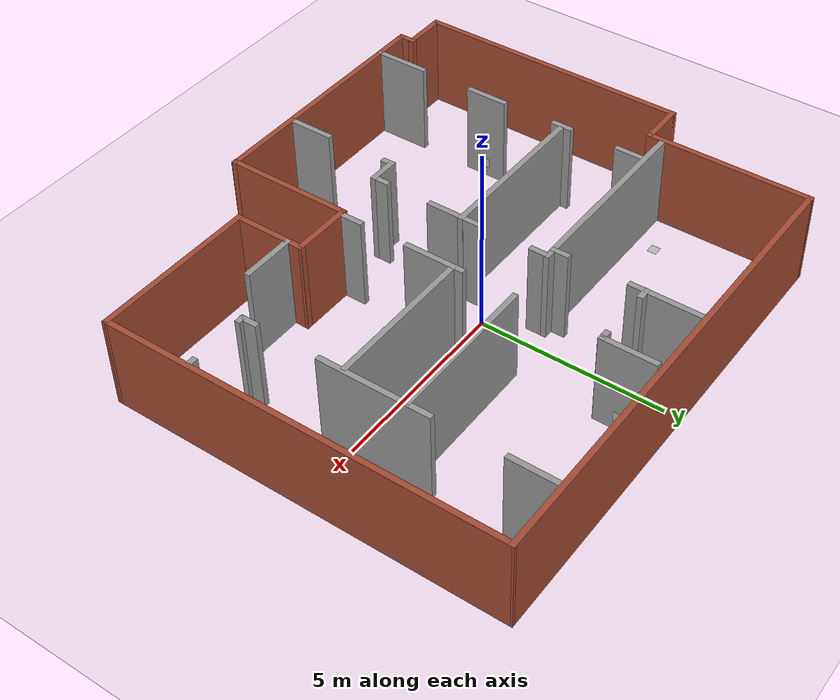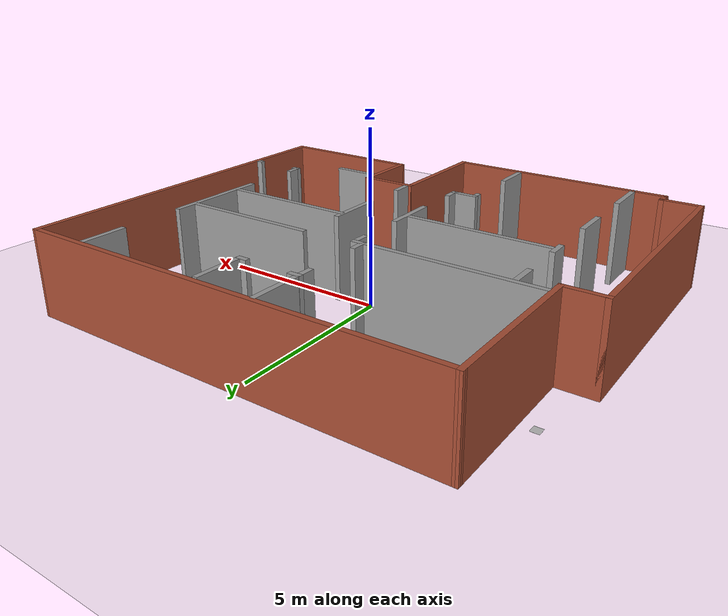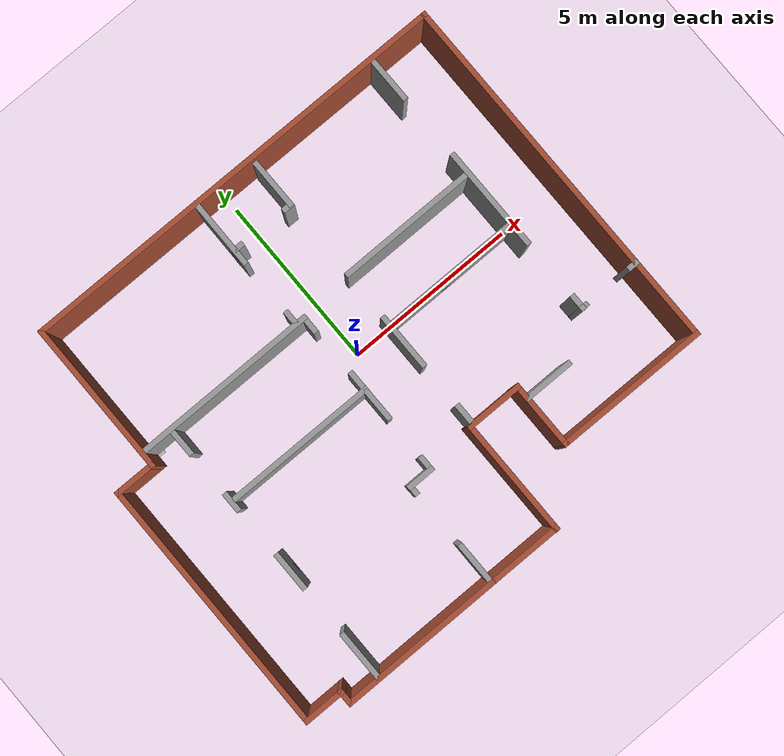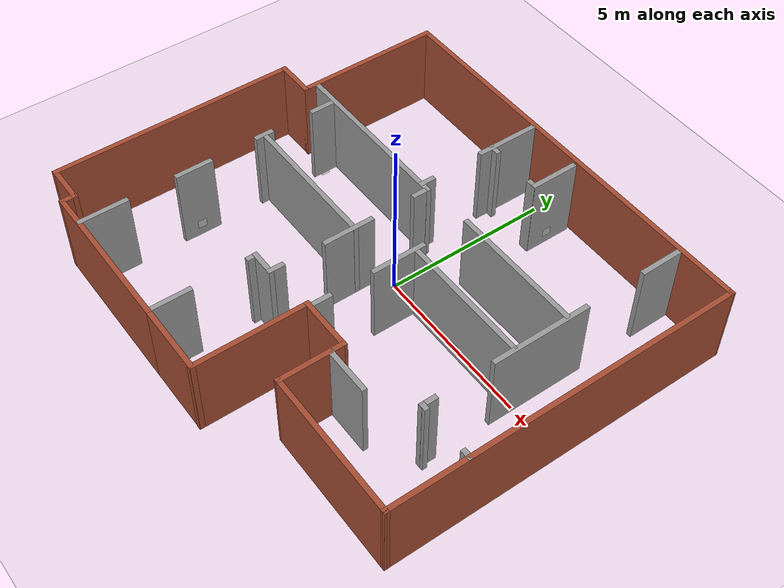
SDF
<sdf version="1.7">
 <world name="default">
  <light name="sun" type="directional">
   <pose>0 0 10 0 -0 0</pose>
   <diffuse>0.8 0.8 0.8 1</diffuse>
   <specular>0.2 0.2 0.2 1</specular>
   <attenuation>
    <range>1000</range>
    <constant>0.9</constant>
    <linear>0.01</linear>
    <quadratic>0.001</quadratic>
   </attenuation>
   <direction>-0.5 0.1 -0.9</direction>
   <spot><inner_angle>0</inner_angle><outer_angle>0</outer_angle><falloff>0</falloff></spot>
  </light>
  <model name="ground_plane">
   <static>1</static>
   <link name="link">
    <collision name="collision">
     <geometry><plane><normal>0 0 1</normal><size>100 100</size></plane></geometry>
     <surface>
      <contact><collide_bitmask>65535</collide_bitmask></contact>
      <friction><ode><mu>100</mu><mu2>50</mu2></ode></friction>
     </surface>
    </collision>
    <visual name="visual">
     <cast_shadows>0</cast_shadows>
     <geometry><plane><normal>0 0 1</normal><size>100 100</size></plane></geometry>
     <material>
      <script><uri>file://media/materials/scripts/gazebo.material</uri><name>Gazebo/Grey</name></script>
     </material>
    </visual>
   </link>
  </model>
  <gravity>0 0 -9.8</gravity>
  <magnetic_field>6e-06 2.3e-05 -4.2e-05</magnetic_field>
  <atmosphere type="adiabatic"/>
  <physics type="ode">
   <max_step_size>0.001</max_step_size>
   <real_time_factor>1</real_time_factor>
   <real_time_update_rate>1000</real_time_update_rate>
  </physics>
  <scene><ambient>0.4 0.4 0.4 1</ambient><background>0.7 0.7 0.7 1</background><shadows>1</shadows></scene>
  <spherical_coordinates>
   <surface_model>EARTH_WGS84</surface_model>
   <latitude_deg>0</latitude_deg>
   <longitude_deg>0</longitude_deg>
   <elevation>0</elevation>
   <heading_deg>0</heading_deg>
  </spherical_coordinates>
  <model name="Building_2">
   <link name="Wall_0">
    <pose>0.975539 -4.38291 0 0 0 -1.5708</pose>
    <inertial>
     <inertia><ixx>0</ixx><ixy>0</ixy><ixz>0</ixz><iyy>0</iyy><iyz>0</iyz><izz>0</izz></inertia>
     <mass>0</mass>
    </inertial>
    <visual name="Wall_0_Visual">
     <pose>0 0 1.25 0 -0 0</pose>
     <geometry><box><size>3.44775 0.15 2.5</size></box></geometry>
     <material>
      <script><uri>file://media/materials/scripts/gazebo.material</uri><name>Gazebo/Bricks</name></script>
      <ambient>1 1 1 1</ambient>
      <shader type="pixel"/>
     </material>
     <meta><layer>0</layer></meta>
    </visual>
    <collision name="Wall_0_Collision">
     <pose>0 0 1.25 0 -0 0</pose>
     <geometry><box><size>3.44775 0.15 2.5</size></box></geometry>
     <surface>
      <friction>
       <ode><mu>1</mu><mu2>1</mu2><fdir1>0 0 0</fdir1><slip1>0</slip1><slip2>0</slip2></ode>
       <torsional>
        <coefficient>1</coefficient>
        <patch_radius>0</patch_radius>
        <surface_radius>0</surface_radius>
        <use_patch_radius>1</use_patch_radius>
        <ode><slip>0</slip></ode>
       </torsional>
      </friction>
      <bounce><restitution_coefficient>0</restitution_coefficient><threshold>1e+06</threshold></bounce>
      <contact>
       <collide_without_contact>0</collide_without_contact>
       <collide_without_contact_bitmask>1</collide_without_contact_bitmask>
       <collide_bitmask>1</collide_bitmask>
       <ode>
        <soft_cfm>0</soft_cfm>
        <soft_erp>0.2</soft_erp>
        <kp>1e+13</kp>
        <kd>1</kd>
        <max_vel>0.01</max_vel>
        <min_depth>0</min_depth>
       </ode>
       <bullet>
        <split_impulse>1</split_impulse>
        <split_impulse_penetration_threshold>-0.01</split_impulse_penetration_threshold>
        <soft_cfm>0</soft_cfm>
        <soft_erp>0.2</soft_erp>
        <kp>1e+13</kp>
        <kd>1</kd>
       </bullet>
      </contact>
     </surface>
    </collision>
   </link>
   <link name="Wall_1">
    <pose>-0.074462 -6.02302 0 0 -0 3.14159</pose>
    <visual name="Wall_1_Visual">
     <pose>0 0 1.25 0 -0 0</pose>
     <geometry><box><size>2.25 0.15 2.5</size></box></geometry>
     <material>
      <script><uri>file://media/materials/scripts/gazebo.material</uri><name>Gazebo/Bricks</name></script>
      <ambient>1 1 1 1</ambient>
      <shader type="pixel"/>
     </material>
     <meta><layer>0</layer></meta>
    </visual>
    <collision name="Wall_1_Collision">
     <pose>0 0 1.25 0 -0 0</pose>
     <geometry><box><size>2.25 0.15 2.5</size></box></geometry>
     <surface>
      <friction>
       <ode><mu>1</mu><mu2>1</mu2><fdir1>0 0 0</fdir1><slip1>0</slip1><slip2>0</slip2></ode>
       <torsional>
        <coefficient>1</coefficient>
        <patch_radius>0</patch_radius>
        <surface_radius>0</surface_radius>
        <use_patch_radius>1</use_patch_radius>
        <ode><slip>0</slip></ode>
       </torsional>
      </friction>
      <bounce><restitution_coefficient>0</restitution_coefficient><threshold>1e+06</threshold></bounce>
      <contact>
       <collide_without_contact>0</collide_without_contact>
       <collide_without_contact_bitmask>1</collide_without_contact_bitmask>
       <collide_bitmask>1</collide_bitmask>
       <ode>
        <soft_cfm>0</soft_cfm>
        <soft_erp>0.2</soft_erp>
        <kp>1e+13</kp>
        <kd>1</kd>
        <max_vel>0.01</max_vel>
        <min_depth>0</min_depth>
       </ode>
       <bullet>
        <split_impulse>1</split_impulse>
        <split_impulse_penetration_threshold>-0.01</split_impulse_penetration_threshold>
        <soft_cfm>0</soft_cfm>
        <soft_erp>0.2</soft_erp>
        <kp>1e+13</kp>
        <kd>1</kd>
       </bullet>
      </contact>
     </surface>
    </collision>
   </link>
   <link name="Wall_10">
    <pose>-5.72446 3.84994 0 0 -0 1.5708</pose>
    <visual name="Wall_10_Visual">
     <pose>0 0 1.25 0 -0 0</pose>
     <geometry><box><size>4.5 0.15 2.5</size></box></geometry>
     <material>
      <script><uri>file://media/materials/scripts/gazebo.material</uri><name>Gazebo/Bricks</name></script>
      <ambient>1 1 1 1</ambient>
      <shader type="pixel"/>
     </material>
     <meta><layer>0</layer></meta>
    </visual>
    <collision name="Wall_10_Collision">
     <pose>0 0 1.25 0 -0 0</pose>
     <geometry><box><size>4.5 0.15 2.5</size></box></geometry>
     <surface>
      <friction>
       <ode><mu>1</mu><mu2>1</mu2><fdir1>0 0 0</fdir1><slip1>0</slip1><slip2>0</slip2></ode>
       <torsional>
        <coefficient>1</coefficient>
        <patch_radius>0</patch_radius>
        <surface_radius>0</surface_radius>
        <use_patch_radius>1</use_patch_radius>
        <ode><slip>0</slip></ode>
       </torsional>
      </friction>
      <bounce><restitution_coefficient>0</restitution_coefficient><threshold>1e+06</threshold></bounce>
      <contact>
       <collide_without_contact>0</collide_without_contact>
       <collide_without_contact_bitmask>1</collide_without_contact_bitmask>
       <collide_bitmask>1</collide_bitmask>
       <ode>
        <soft_cfm>0</soft_cfm>
        <soft_erp>0.2</soft_erp>
        <kp>1e+13</kp>
        <kd>1</kd>
        <max_vel>0.01</max_vel>
        <min_depth>0</min_depth>
       </ode>
       <bullet>
        <split_impulse>1</split_impulse>
        <split_impulse_penetration_threshold>-0.01</split_impulse_penetration_threshold>
        <soft_cfm>0</soft_cfm>
        <soft_erp>0.2</soft_erp>
        <kp>1e+13</kp>
        <kd>1</kd>
       </bullet>
      </contact>
     </surface>
    </collision>
   </link>
   <link name="Wall_11">
    <pose>0.54984 6.01575 0 0 0 -0.001465</pose>
    <visual name="Wall_11_Visual">
     <pose>0 0 1.25 0 -0 0</pose>
     <geometry><box><size>12.6986 0.15 2.5</size></box></geometry>
     <material>
      <script><uri>file://media/materials/scripts/gazebo.material</uri><name>Gazebo/Bricks</name></script>
      <ambient>1 1 1 1</ambient>
      <shader type="pixel"/>
     </material>
     <meta><layer>0</layer></meta>
    </visual>
    <collision name="Wall_11_Collision">
     <pose>0 0 1.25 0 -0 0</pose>
     <geometry><box><size>12.6986 0.15 2.5</size></box></geometry>
     <surface>
      <friction>
       <ode><mu>1</mu><mu2>1</mu2><fdir1>0 0 0</fdir1><slip1>0</slip1><slip2>0</slip2></ode>
       <torsional>
        <coefficient>1</coefficient>
        <patch_radius>0</patch_radius>
        <surface_radius>0</surface_radius>
        <use_patch_radius>1</use_patch_radius>
        <ode><slip>0</slip></ode>
       </torsional>
      </friction>
      <bounce><restitution_coefficient>0</restitution_coefficient><threshold>1e+06</threshold></bounce>
      <contact>
       <collide_without_contact>0</collide_without_contact>
       <collide_without_contact_bitmask>1</collide_without_contact_bitmask>
       <collide_bitmask>1</collide_bitmask>
       <ode>
        <soft_cfm>0</soft_cfm>
        <soft_erp>0.2</soft_erp>
        <kp>1e+13</kp>
        <kd>1</kd>
        <max_vel>0.01</max_vel>
        <min_depth>0</min_depth>
       </ode>
       <bullet>
        <split_impulse>1</split_impulse>
        <split_impulse_penetration_threshold>-0.01</split_impulse_penetration_threshold>
        <soft_cfm>0</soft_cfm>
        <soft_erp>0.2</soft_erp>
        <kp>1e+13</kp>
        <kd>1</kd>
       </bullet>
      </contact>
     </surface>
    </collision>
   </link>
   <link name="Wall_14">
    <pose>6.82414 0.706559 0 0 0 -1.5708</pose>
    <visual name="Wall_14_Visual">
     <pose>0 0 1.25 0 -0 0</pose>
     <geometry><box><size>10.75 0.15 2.5</size></box></geometry>
     <material>
      <script><uri>file://media/materials/scripts/gazebo.material</uri><name>Gazebo/Bricks</name></script>
      <ambient>1 1 1 1</ambient>
      <shader type="pixel"/>
     </material>
     <meta><layer>0</layer></meta>
    </visual>
    <collision name="Wall_14_Collision">
     <pose>0 0 1.25 0 -0 0</pose>
     <geometry><box><size>10.75 0.15 2.5</size></box></geometry>
     <surface>
      <friction>
       <ode><mu>1</mu><mu2>1</mu2><fdir1>0 0 0</fdir1><slip1>0</slip1><slip2>0</slip2></ode>
       <torsional>
        <coefficient>1</coefficient>
        <patch_radius>0</patch_radius>
        <surface_radius>0</surface_radius>
        <use_patch_radius>1</use_patch_radius>
        <ode><slip>0</slip></ode>
       </torsional>
      </friction>
      <bounce><restitution_coefficient>0</restitution_coefficient><threshold>1e+06</threshold></bounce>
      <contact>
       <collide_without_contact>0</collide_without_contact>
       <collide_without_contact_bitmask>1</collide_without_contact_bitmask>
       <collide_bitmask>1</collide_bitmask>
       <ode>
        <soft_cfm>0</soft_cfm>
        <soft_erp>0.2</soft_erp>
        <kp>1e+13</kp>
        <kd>1</kd>
        <max_vel>0.01</max_vel>
        <min_depth>0</min_depth>
       </ode>
       <bullet>
        <split_impulse>1</split_impulse>
        <split_impulse_penetration_threshold>-0.01</split_impulse_penetration_threshold>
        <soft_cfm>0</soft_cfm>
        <soft_erp>0.2</soft_erp>
        <kp>1e+13</kp>
        <kd>1</kd>
       </bullet>
      </contact>
     </surface>
    </collision>
   </link>
   <link name="Wall_15">
    <pose>4.67484 -4.58425 0 0 -0 3.13732</pose>
    <visual name="Wall_15_Visual">
     <pose>0 0 1.25 0 -0 0</pose>
     <geometry><box><size>4.44864 0.15 2.5</size></box></geometry>
     <material>
      <script><uri>file://media/materials/scripts/gazebo.material</uri><name>Gazebo/Bricks</name></script>
      <ambient>1 1 1 1</ambient>
      <shader type="pixel"/>
     </material>
     <meta><layer>0</layer></meta>
    </visual>
    <collision name="Wall_15_Collision">
     <pose>0 0 1.25 0 -0 0</pose>
     <geometry><box><size>4.44864 0.15 2.5</size></box></geometry>
     <surface>
      <friction>
       <ode><mu>1</mu><mu2>1</mu2><fdir1>0 0 0</fdir1><slip1>0</slip1><slip2>0</slip2></ode>
       <torsional>
        <coefficient>1</coefficient>
        <patch_radius>0</patch_radius>
        <surface_radius>0</surface_radius>
        <use_patch_radius>1</use_patch_radius>
        <ode><slip>0</slip></ode>
       </torsional>
      </friction>
      <bounce><restitution_coefficient>0</restitution_coefficient><threshold>1e+06</threshold></bounce>
      <contact>
       <collide_without_contact>0</collide_without_contact>
       <collide_without_contact_bitmask>1</collide_without_contact_bitmask>
       <collide_bitmask>1</collide_bitmask>
       <ode>
        <soft_cfm>0</soft_cfm>
        <soft_erp>0.2</soft_erp>
        <kp>1e+13</kp>
        <kd>1</kd>
        <max_vel>0.01</max_vel>
        <min_depth>0</min_depth>
       </ode>
       <bullet>
        <split_impulse>1</split_impulse>
        <split_impulse_penetration_threshold>-0.01</split_impulse_penetration_threshold>
        <soft_cfm>0</soft_cfm>
        <soft_erp>0.2</soft_erp>
        <kp>1e+13</kp>
        <kd>1</kd>
       </bullet>
      </contact>
     </surface>
    </collision>
   </link>
   <link name="Wall_16">
    <pose>2.52554 -3.64508 0 0 -0 1.5708</pose>
    <visual name="Wall_16_Visual">
     <pose>0 0 1.25 0 -0 0</pose>
     <geometry><box><size>2.00994 0.15 2.5</size></box></geometry>
     <material>
      <script><uri>file://media/materials/scripts/gazebo.material</uri><name>Gazebo/Bricks</name></script>
      <ambient>1 1 1 1</ambient>
      <shader type="pixel"/>
     </material>
     <meta><layer>0</layer></meta>
    </visual>
    <collision name="Wall_16_Collision">
     <pose>0 0 1.25 0 -0 0</pose>
     <geometry><box><size>2.00994 0.15 2.5</size></box></geometry>
     <surface>
      <friction>
       <ode><mu>1</mu><mu2>1</mu2><fdir1>0 0 0</fdir1><slip1>0</slip1><slip2>0</slip2></ode>
       <torsional>
        <coefficient>1</coefficient>
        <patch_radius>0</patch_radius>
        <surface_radius>0</surface_radius>
        <use_patch_radius>1</use_patch_radius>
        <ode><slip>0</slip></ode>
       </torsional>
      </friction>
      <bounce><restitution_coefficient>0</restitution_coefficient><threshold>1e+06</threshold></bounce>
      <contact>
       <collide_without_contact>0</collide_without_contact>
       <collide_without_contact_bitmask>1</collide_without_contact_bitmask>
       <collide_bitmask>1</collide_bitmask>
       <ode>
        <soft_cfm>0</soft_cfm>
        <soft_erp>0.2</soft_erp>
        <kp>1e+13</kp>
        <kd>1</kd>
        <max_vel>0.01</max_vel>
        <min_depth>0</min_depth>
       </ode>
       <bullet>
        <split_impulse>1</split_impulse>
        <split_impulse_penetration_threshold>-0.01</split_impulse_penetration_threshold>
        <soft_cfm>0</soft_cfm>
        <soft_erp>0.2</soft_erp>
        <kp>1e+13</kp>
        <kd>1</kd>
       </bullet>
      </contact>
     </surface>
    </collision>
   </link>
   <link name="Wall_17">
    <pose>1.75059 -2.71926 0 0 -0 3.14053</pose>
    <visual name="Wall_17_Visual">
     <pose>0 0 1.25 0 -0 0</pose>
     <geometry><box><size>1.69991 0.15 2.5</size></box></geometry>
     <material>
      <script><uri>file://media/materials/scripts/gazebo.material</uri><name>Gazebo/Bricks</name></script>
      <ambient>1 1 1 1</ambient>
      <shader type="pixel"/>
     </material>
     <meta><layer>0</layer></meta>
    </visual>
    <collision name="Wall_17_Collision">
     <pose>0 0 1.25 0 -0 0</pose>
     <geometry><box><size>1.69991 0.15 2.5</size></box></geometry>
     <surface>
      <friction>
       <ode><mu>1</mu><mu2>1</mu2><fdir1>0 0 0</fdir1><slip1>0</slip1><slip2>0</slip2></ode>
       <torsional>
        <coefficient>1</coefficient>
        <patch_radius>0</patch_radius>
        <surface_radius>0</surface_radius>
        <use_patch_radius>1</use_patch_radius>
        <ode><slip>0</slip></ode>
       </torsional>
      </friction>
      <bounce><restitution_coefficient>0</restitution_coefficient><threshold>1e+06</threshold></bounce>
      <contact>
       <collide_without_contact>0</collide_without_contact>
       <collide_without_contact_bitmask>1</collide_without_contact_bitmask>
       <collide_bitmask>1</collide_bitmask>
       <ode>
        <soft_cfm>0</soft_cfm>
        <soft_erp>0.2</soft_erp>
        <kp>1e+13</kp>
        <kd>1</kd>
        <max_vel>0.01</max_vel>
        <min_depth>0</min_depth>
       </ode>
       <bullet>
        <split_impulse>1</split_impulse>
        <split_impulse_penetration_threshold>-0.01</split_impulse_penetration_threshold>
        <soft_cfm>0</soft_cfm>
        <soft_erp>0.2</soft_erp>
        <kp>1e+13</kp>
        <kd>1</kd>
       </bullet>
      </contact>
     </surface>
    </collision>
   </link>
   <link name="Wall_19">
    <pose>-4.78364 -5.32139 0 0 -0 1.5708</pose>
    <visual name="Wall_19_Visual">
     <pose>0 0 1.25 0 -0 0</pose>
     <geometry><box><size>1.5 0.15 2.5</size></box></geometry>
     <material>
      <script><uri>file://media/materials/scripts/gazebo.material</uri><name>Gazebo/Grey</name></script>
      <ambient>1 1 1 1</ambient>
      <shader type="pixel"/>
     </material>
     <meta><layer>0</layer></meta>
    </visual>
    <collision name="Wall_19_Collision">
     <pose>0 0 1.25 0 -0 0</pose>
     <geometry><box><size>1.5 0.15 2.5</size></box></geometry>
     <surface>
      <friction>
       <ode><mu>1</mu><mu2>1</mu2><fdir1>0 0 0</fdir1><slip1>0</slip1><slip2>0</slip2></ode>
       <torsional>
        <coefficient>1</coefficient>
        <patch_radius>0</patch_radius>
        <surface_radius>0</surface_radius>
        <use_patch_radius>1</use_patch_radius>
        <ode><slip>0</slip></ode>
       </torsional>
      </friction>
      <bounce><restitution_coefficient>0</restitution_coefficient><threshold>1e+06</threshold></bounce>
      <contact>
       <collide_without_contact>0</collide_without_contact>
       <collide_without_contact_bitmask>1</collide_without_contact_bitmask>
       <collide_bitmask>1</collide_bitmask>
       <ode>
        <soft_cfm>0</soft_cfm>
        <soft_erp>0.2</soft_erp>
        <kp>1e+13</kp>
        <kd>1</kd>
        <max_vel>0.01</max_vel>
        <min_depth>0</min_depth>
       </ode>
       <bullet>
        <split_impulse>1</split_impulse>
        <split_impulse_penetration_threshold>-0.01</split_impulse_penetration_threshold>
        <soft_cfm>0</soft_cfm>
        <soft_erp>0.2</soft_erp>
        <kp>1e+13</kp>
        <kd>1</kd>
       </bullet>
      </contact>
     </surface>
    </collision>
   </link>
   <link name="Wall_23">
    <pose>-4.77837 -2.58462 0 0 -0 1.5708</pose>
    <inertial>
     <inertia><ixx>0</ixx><ixy>0</ixy><ixz>0</ixz><iyy>0</iyy><iyz>0</iyz><izz>0</izz></inertia>
     <mass>0</mass>
    </inertial>
    <visual name="Wall_23_Visual">
     <pose>0 0 1.25 0 -0 0</pose>
     <geometry><box><size>1.15111 0.15 2.5</size></box></geometry>
     <material>
      <script><uri>file://media/materials/scripts/gazebo.material</uri><name>Gazebo/Grey</name></script>
      <ambient>1 1 1 1</ambient>
      <shader type="pixel"/>
     </material>
     <meta><layer>0</layer></meta>
    </visual>
    <collision name="Wall_23_Collision">
     <pose>0 0 1.25 0 -0 0</pose>
     <geometry><box><size>1.15111 0.15 2.5</size></box></geometry>
     <surface>
      <friction>
       <ode><mu>1</mu><mu2>1</mu2><fdir1>0 0 0</fdir1><slip1>0</slip1><slip2>0</slip2></ode>
       <torsional>
        <coefficient>1</coefficient>
        <patch_radius>0</patch_radius>
        <surface_radius>0</surface_radius>
        <use_patch_radius>1</use_patch_radius>
        <ode><slip>0</slip></ode>
       </torsional>
      </friction>
      <bounce><restitution_coefficient>0</restitution_coefficient><threshold>1e+06</threshold></bounce>
      <contact>
       <collide_without_contact>0</collide_without_contact>
       <collide_without_contact_bitmask>1</collide_without_contact_bitmask>
       <collide_bitmask>1</collide_bitmask>
       <ode>
        <soft_cfm>0</soft_cfm>
        <soft_erp>0.2</soft_erp>
        <kp>1e+13</kp>
        <kd>1</kd>
        <max_vel>0.01</max_vel>
        <min_depth>0</min_depth>
       </ode>
       <bullet>
        <split_impulse>1</split_impulse>
        <split_impulse_penetration_threshold>-0.01</split_impulse_penetration_threshold>
        <soft_cfm>0</soft_cfm>
        <soft_erp>0.2</soft_erp>
        <kp>1e+13</kp>
        <kd>1</kd>
       </bullet>
      </contact>
     </surface>
    </collision>
   </link>
   <link name="Wall_25">
    <pose>-4.79341 -0.321482 0 0 -0 1.5708</pose>
    <visual name="Wall_25_Visual">
     <pose>0 0 1.25 0 -0 0</pose>
     <geometry><box><size>0.586087 0.15 2.5</size></box></geometry>
     <material>
      <script><uri>file://media/materials/scripts/gazebo.material</uri><name>Gazebo/Grey</name></script>
      <ambient>1 1 1 1</ambient>
      <shader type="pixel"/>
     </material>
     <meta><layer>0</layer></meta>
    </visual>
    <collision name="Wall_25_Collision">
     <pose>0 0 1.25 0 -0 0</pose>
     <geometry><box><size>0.586087 0.15 2.5</size></box></geometry>
     <surface>
      <friction>
       <ode><mu>1</mu><mu2>1</mu2><fdir1>0 0 0</fdir1><slip1>0</slip1><slip2>0</slip2></ode>
       <torsional>
        <coefficient>1</coefficient>
        <patch_radius>0</patch_radius>
        <surface_radius>0</surface_radius>
        <use_patch_radius>1</use_patch_radius>
        <ode><slip>0</slip></ode>
       </torsional>
      </friction>
      <bounce><restitution_coefficient>0</restitution_coefficient><threshold>1e+06</threshold></bounce>
      <contact>
       <collide_without_contact>0</collide_without_contact>
       <collide_without_contact_bitmask>1</collide_without_contact_bitmask>
       <collide_bitmask>1</collide_bitmask>
       <ode>
        <soft_cfm>0</soft_cfm>
        <soft_erp>0.2</soft_erp>
        <kp>1e+13</kp>
        <kd>1</kd>
        <max_vel>0.01</max_vel>
        <min_depth>0</min_depth>
       </ode>
       <bullet>
        <split_impulse>1</split_impulse>
        <split_impulse_penetration_threshold>-0.01</split_impulse_penetration_threshold>
        <soft_cfm>0</soft_cfm>
        <soft_erp>0.2</soft_erp>
        <kp>1e+13</kp>
        <kd>1</kd>
       </bullet>
      </contact>
     </surface>
    </collision>
   </link>
   <link name="Wall_27">
    <pose>-4.80309 1.60581 0 0 -0 1.5708</pose>
    <inertial>
     <inertia><ixx>0</ixx><ixy>0</ixy><ixz>0</ixz><iyy>0</iyy><iyz>0</iyz><izz>0</izz></inertia>
     <mass>0</mass>
    </inertial>
    <visual name="Wall_27_Visual">
     <pose>0 0 1.25 0 -0 0</pose>
     <geometry><box><size>0.757541 0.15 2.5</size></box></geometry>
     <material>
      <script><uri>file://media/materials/scripts/gazebo.material</uri><name>Gazebo/Grey</name></script>
      <ambient>1 1 1 1</ambient>
      <shader type="pixel"/>
     </material>
     <meta><layer>0</layer></meta>
    </visual>
    <collision name="Wall_27_Collision">
     <pose>0 0 1.25 0 -0 0</pose>
     <geometry><box><size>0.757541 0.15 2.5</size></box></geometry>
     <surface>
      <friction>
       <ode><mu>1</mu><mu2>1</mu2><fdir1>0 0 0</fdir1><slip1>0</slip1><slip2>0</slip2></ode>
       <torsional>
        <coefficient>1</coefficient>
        <patch_radius>0</patch_radius>
        <surface_radius>0</surface_radius>
        <use_patch_radius>1</use_patch_radius>
        <ode><slip>0</slip></ode>
       </torsional>
      </friction>
      <bounce><restitution_coefficient>0</restitution_coefficient><threshold>1e+06</threshold></bounce>
      <contact>
       <collide_without_contact>0</collide_without_contact>
       <collide_without_contact_bitmask>1</collide_without_contact_bitmask>
       <collide_bitmask>1</collide_bitmask>
       <ode>
        <soft_cfm>0</soft_cfm>
        <soft_erp>0.2</soft_erp>
        <kp>1e+13</kp>
        <kd>1</kd>
        <max_vel>0.01</max_vel>
        <min_depth>0</min_depth>
       </ode>
       <bullet>
        <split_impulse>1</split_impulse>
        <split_impulse_penetration_threshold>-0.01</split_impulse_penetration_threshold>
        <soft_cfm>0</soft_cfm>
        <soft_erp>0.2</soft_erp>
        <kp>1e+13</kp>
        <kd>1</kd>
       </bullet>
      </contact>
     </surface>
    </collision>
   </link>
   <link name="Wall_29">
    <pose>-3.01821 2.05691 0 0 -0 0</pose>
    <inertial>
     <inertia><ixx>0</ixx><ixy>0</ixy><ixz>0</ixz><iyy>0</iyy><iyz>0</iyz><izz>0</izz></inertia>
     <mass>0</mass>
    </inertial>
    <visual name="Wall_29_Visual">
     <pose>0 0 1.25 0 -0 0</pose>
     <geometry><box><size>5.27655 0.15 2.5</size></box></geometry>
     <material>
      <script><uri>file://media/materials/scripts/gazebo.material</uri><name>Gazebo/Grey</name></script>
      <ambient>1 1 1 1</ambient>
      <shader type="pixel"/>
     </material>
     <meta><layer>0</layer></meta>
    </visual>
    <collision name="Wall_29_Collision">
     <pose>0 0 1.25 0 -0 0</pose>
     <geometry><box><size>5.27655 0.15 2.5</size></box></geometry>
     <surface>
      <friction>
       <ode><mu>1</mu><mu2>1</mu2><fdir1>0 0 0</fdir1><slip1>0</slip1><slip2>0</slip2></ode>
       <torsional>
        <coefficient>1</coefficient>
        <patch_radius>0</patch_radius>
        <surface_radius>0</surface_radius>
        <use_patch_radius>1</use_patch_radius>
        <ode><slip>0</slip></ode>
       </torsional>
      </friction>
      <bounce><restitution_coefficient>0</restitution_coefficient><threshold>1e+06</threshold></bounce>
      <contact>
       <collide_without_contact>0</collide_without_contact>
       <collide_without_contact_bitmask>1</collide_without_contact_bitmask>
       <collide_bitmask>1</collide_bitmask>
       <ode>
        <soft_cfm>0</soft_cfm>
        <soft_erp>0.2</soft_erp>
        <kp>1e+13</kp>
        <kd>1</kd>
        <max_vel>0.01</max_vel>
        <min_depth>0</min_depth>
       </ode>
       <bullet>
        <split_impulse>1</split_impulse>
        <split_impulse_penetration_threshold>-0.01</split_impulse_penetration_threshold>
        <soft_cfm>0</soft_cfm>
        <soft_erp>0.2</soft_erp>
        <kp>1e+13</kp>
        <kd>1</kd>
       </bullet>
      </contact>
     </surface>
    </collision>
   </link>
   <link name="Wall_30">
    <pose>-0.459211 1.7956 0 0 0 -1.5708</pose>
    <inertial>
     <inertia><ixx>0</ixx><ixy>0</ixy><ixz>0</ixz><iyy>0</iyy><iyz>0</iyz><izz>0</izz></inertia>
     <mass>0</mass>
    </inertial>
    <visual name="Wall_30_Visual">
     <pose>0 0 1.25 0 -0 0</pose>
     <geometry><box><size>0.445654 0.15 2.5</size></box></geometry>
     <material>
      <script><uri>file://media/materials/scripts/gazebo.material</uri><name>Gazebo/Grey</name></script>
      <ambient>1 1 1 1</ambient>
      <shader type="pixel"/>
     </material>
     <meta><layer>0</layer></meta>
    </visual>
    <collision name="Wall_30_Collision">
     <pose>0 0 1.25 0 -0 0</pose>
     <geometry><box><size>0.445654 0.15 2.5</size></box></geometry>
     <surface>
      <friction>
       <ode><mu>1</mu><mu2>1</mu2><fdir1>0 0 0</fdir1><slip1>0</slip1><slip2>0</slip2></ode>
       <torsional>
        <coefficient>1</coefficient>
        <patch_radius>0</patch_radius>
        <surface_radius>0</surface_radius>
        <use_patch_radius>1</use_patch_radius>
        <ode><slip>0</slip></ode>
       </torsional>
      </friction>
      <bounce><restitution_coefficient>0</restitution_coefficient><threshold>1e+06</threshold></bounce>
      <contact>
       <collide_without_contact>0</collide_without_contact>
       <collide_without_contact_bitmask>1</collide_without_contact_bitmask>
       <collide_bitmask>1</collide_bitmask>
       <ode>
        <soft_cfm>0</soft_cfm>
        <soft_erp>0.2</soft_erp>
        <kp>1e+13</kp>
        <kd>1</kd>
        <max_vel>0.01</max_vel>
        <min_depth>0</min_depth>
       </ode>
       <bullet>
        <split_impulse>1</split_impulse>
        <split_impulse_penetration_threshold>-0.01</split_impulse_penetration_threshold>
        <soft_cfm>0</soft_cfm>
        <soft_erp>0.2</soft_erp>
        <kp>1e+13</kp>
        <kd>1</kd>
       </bullet>
      </contact>
     </surface>
    </collision>
   </link>
   <link name="Wall_33">
    <pose>-0.445665 -0.504153 0 0 0 -1.5708</pose>
    <inertial>
     <inertia><ixx>0</ixx><ixy>0</ixy><ixz>0</ixz><iyy>0</iyy><iyz>0</iyz><izz>0</izz></inertia>
     <mass>0</mass>
    </inertial>
    <visual name="Wall_33_Visual">
     <pose>0 0 1.25 0 -0 0</pose>
     <geometry><box><size>1.56049 0.15 2.5</size></box></geometry>
     <material>
      <script><uri>file://media/materials/scripts/gazebo.material</uri><name>Gazebo/Grey</name></script>
      <ambient>1 1 1 1</ambient>
      <shader type="pixel"/>
     </material>
     <meta><layer>0</layer></meta>
    </visual>
    <collision name="Wall_33_Collision">
     <pose>0 0 1.25 0 -0 0</pose>
     <geometry><box><size>1.56049 0.15 2.5</size></box></geometry>
     <surface>
      <friction>
       <ode><mu>1</mu><mu2>1</mu2><fdir1>0 0 0</fdir1><slip1>0</slip1><slip2>0</slip2></ode>
       <torsional>
        <coefficient>1</coefficient>
        <patch_radius>0</patch_radius>
        <surface_radius>0</surface_radius>
        <use_patch_radius>1</use_patch_radius>
        <ode><slip>0</slip></ode>
       </torsional>
      </friction>
      <bounce><restitution_coefficient>0</restitution_coefficient><threshold>1e+06</threshold></bounce>
      <contact>
       <collide_without_contact>0</collide_without_contact>
       <collide_without_contact_bitmask>1</collide_without_contact_bitmask>
       <collide_bitmask>1</collide_bitmask>
       <ode>
        <soft_cfm>0</soft_cfm>
        <soft_erp>0.2</soft_erp>
        <kp>1e+13</kp>
        <kd>1</kd>
        <max_vel>0.01</max_vel>
        <min_depth>0</min_depth>
       </ode>
       <bullet>
        <split_impulse>1</split_impulse>
        <split_impulse_penetration_threshold>-0.01</split_impulse_penetration_threshold>
        <soft_cfm>0</soft_cfm>
        <soft_erp>0.2</soft_erp>
        <kp>1e+13</kp>
        <kd>1</kd>
       </bullet>
      </contact>
     </surface>
    </collision>
   </link>
   <link name="Wall_36">
    <pose>-2.55225 -0.313301 0 0 -0 3.14002</pose>
    <inertial>
     <inertia><ixx>0</ixx><ixy>0</ixy><ixz>0</ixz><iyy>0</iyy><iyz>0</iyz><izz>0</izz></inertia>
     <mass>0</mass>
    </inertial>
    <visual name="Wall_36_Visual">
     <pose>0 0 1.25 0 -0 0</pose>
     <geometry><box><size>4.36835 0.15 2.5</size></box></geometry>
     <material>
      <script><uri>file://media/materials/scripts/gazebo.material</uri><name>Gazebo/Grey</name></script>
      <ambient>1 1 1 1</ambient>
      <shader type="pixel"/>
     </material>
     <meta><layer>0</layer></meta>
    </visual>
    <collision name="Wall_36_Collision">
     <pose>0 0 1.25 0 -0 0</pose>
     <geometry><box><size>4.36835 0.15 2.5</size></box></geometry>
     <surface>
      <friction>
       <ode><mu>1</mu><mu2>1</mu2><fdir1>0 0 0</fdir1><slip1>0</slip1><slip2>0</slip2></ode>
       <torsional>
        <coefficient>1</coefficient>
        <patch_radius>0</patch_radius>
        <surface_radius>0</surface_radius>
        <use_patch_radius>1</use_patch_radius>
        <ode><slip>0</slip></ode>
       </torsional>
      </friction>
      <bounce><restitution_coefficient>0</restitution_coefficient><threshold>1e+06</threshold></bounce>
      <contact>
       <collide_without_contact>0</collide_without_contact>
       <collide_without_contact_bitmask>1</collide_without_contact_bitmask>
       <collide_bitmask>1</collide_bitmask>
       <ode>
        <soft_cfm>0</soft_cfm>
        <soft_erp>0.2</soft_erp>
        <kp>1e+13</kp>
        <kd>1</kd>
        <max_vel>0.01</max_vel>
        <min_depth>0</min_depth>
       </ode>
       <bullet>
        <split_impulse>1</split_impulse>
        <split_impulse_penetration_threshold>-0.01</split_impulse_penetration_threshold>
        <soft_cfm>0</soft_cfm>
        <soft_erp>0.2</soft_erp>
        <kp>1e+13</kp>
        <kd>1</kd>
       </bullet>
      </contact>
     </surface>
    </collision>
   </link>
   <link name="Wall_42">
    <pose>-1.1239 -5.36388 0 0 -0 1.56899</pose>
    <inertial>
     <inertia><ixx>0</ixx><ixy>0</ixy><ixz>0</ixz><iyy>0</iyy><iyz>0</iyz><izz>0</izz></inertia>
     <mass>0</mass>
    </inertial>
    <visual name="Wall_42_Visual">
     <pose>0 0 1.25 0 -0 0</pose>
     <geometry><box><size>1.1746 0.15 2.5</size></box></geometry>
     <material>
      <script><uri>file://media/materials/scripts/gazebo.material</uri><name>Gazebo/Grey</name></script>
      <ambient>1 1 1 1</ambient>
      <shader type="pixel"/>
     </material>
     <meta><layer>0</layer></meta>
    </visual>
    <collision name="Wall_42_Collision">
     <pose>0 0 1.25 0 -0 0</pose>
     <geometry><box><size>1.1746 0.15 2.5</size></box></geometry>
     <surface>
      <friction>
       <ode><mu>1</mu><mu2>1</mu2><fdir1>0 0 0</fdir1><slip1>0</slip1><slip2>0</slip2></ode>
       <torsional>
        <coefficient>1</coefficient>
        <patch_radius>0</patch_radius>
        <surface_radius>0</surface_radius>
        <use_patch_radius>1</use_patch_radius>
        <ode><slip>0</slip></ode>
       </torsional>
      </friction>
      <bounce><restitution_coefficient>0</restitution_coefficient><threshold>1e+06</threshold></bounce>
      <contact>
       <collide_without_contact>0</collide_without_contact>
       <collide_without_contact_bitmask>1</collide_without_contact_bitmask>
       <collide_bitmask>1</collide_bitmask>
       <ode>
        <soft_cfm>0</soft_cfm>
        <soft_erp>0.2</soft_erp>
        <kp>1e+13</kp>
        <kd>1</kd>
        <max_vel>0.01</max_vel>
        <min_depth>0</min_depth>
       </ode>
       <bullet>
        <split_impulse>1</split_impulse>
        <split_impulse_penetration_threshold>-0.01</split_impulse_penetration_threshold>
        <soft_cfm>0</soft_cfm>
        <soft_erp>0.2</soft_erp>
        <kp>1e+13</kp>
        <kd>1</kd>
       </bullet>
      </contact>
     </surface>
    </collision>
   </link>
   <link name="Wall_44">
    <pose>-1.13344 -3.07085 0 0 -0 1.5708</pose>
    <inertial>
     <inertia><ixx>0</ixx><ixy>0</ixy><ixz>0</ixz><iyy>0</iyy><iyz>0</iyz><izz>0</izz></inertia>
     <mass>0</mass>
    </inertial>
    <visual name="Wall_44_Visual">
     <pose>0 0 1.25 0 -0 0</pose>
     <geometry><box><size>0.209166 0.15 2.5</size></box></geometry>
     <material>
      <script><uri>file://media/materials/scripts/gazebo.material</uri><name>Gazebo/Grey</name></script>
      <ambient>1 1 1 1</ambient>
      <shader type="pixel"/>
     </material>
     <meta><layer>0</layer></meta>
    </visual>
    <collision name="Wall_44_Collision">
     <pose>0 0 1.25 0 -0 0</pose>
     <geometry><box><size>0.209166 0.15 2.5</size></box></geometry>
     <surface>
      <friction>
       <ode><mu>1</mu><mu2>1</mu2><fdir1>0 0 0</fdir1><slip1>0</slip1><slip2>0</slip2></ode>
       <torsional>
        <coefficient>1</coefficient>
        <patch_radius>0</patch_radius>
        <surface_radius>0</surface_radius>
        <use_patch_radius>1</use_patch_radius>
        <ode><slip>0</slip></ode>
       </torsional>
      </friction>
      <bounce><restitution_coefficient>0</restitution_coefficient><threshold>1e+06</threshold></bounce>
      <contact>
       <collide_without_contact>0</collide_without_contact>
       <collide_without_contact_bitmask>1</collide_without_contact_bitmask>
       <collide_bitmask>1</collide_bitmask>
       <ode>
        <soft_cfm>0</soft_cfm>
        <soft_erp>0.2</soft_erp>
        <kp>1e+13</kp>
        <kd>1</kd>
        <max_vel>0.01</max_vel>
        <min_depth>0</min_depth>
       </ode>
       <bullet>
        <split_impulse>1</split_impulse>
        <split_impulse_penetration_threshold>-0.01</split_impulse_penetration_threshold>
        <soft_cfm>0</soft_cfm>
        <soft_erp>0.2</soft_erp>
        <kp>1e+13</kp>
        <kd>1</kd>
       </bullet>
      </contact>
     </surface>
    </collision>
   </link>
   <link name="Wall_45">
    <pose>-0.801988 -2.89585 0 0 -0 0</pose>
    <inertial>
     <inertia><ixx>0</ixx><ixy>0</ixy><ixz>0</ixz><iyy>0</iyy><iyz>0</iyz><izz>0</izz></inertia>
     <mass>0</mass>
    </inertial>
    <visual name="Wall_45_Visual">
     <pose>0 0 1.25 0 -0 0</pose>
     <geometry><box><size>0.822962 0.15 2.5</size></box></geometry>
     <material>
      <script><uri>file://media/materials/scripts/gazebo.material</uri><name>Gazebo/Grey</name></script>
      <ambient>1 1 1 1</ambient>
      <shader type="pixel"/>
     </material>
     <meta><layer>0</layer></meta>
    </visual>
    <collision name="Wall_45_Collision">
     <pose>0 0 1.25 0 -0 0</pose>
     <geometry><box><size>0.822962 0.15 2.5</size></box></geometry>
     <surface>
      <friction>
       <ode><mu>1</mu><mu2>1</mu2><fdir1>0 0 0</fdir1><slip1>0</slip1><slip2>0</slip2></ode>
       <torsional>
        <coefficient>1</coefficient>
        <patch_radius>0</patch_radius>
        <surface_radius>0</surface_radius>
        <use_patch_radius>1</use_patch_radius>
        <ode><slip>0</slip></ode>
       </torsional>
      </friction>
      <bounce><restitution_coefficient>0</restitution_coefficient><threshold>1e+06</threshold></bounce>
      <contact>
       <collide_without_contact>0</collide_without_contact>
       <collide_without_contact_bitmask>1</collide_without_contact_bitmask>
       <collide_bitmask>1</collide_bitmask>
       <ode>
        <soft_cfm>0</soft_cfm>
        <soft_erp>0.2</soft_erp>
        <kp>1e+13</kp>
        <kd>1</kd>
        <max_vel>0.01</max_vel>
        <min_depth>0</min_depth>
       </ode>
       <bullet>
        <split_impulse>1</split_impulse>
        <split_impulse_penetration_threshold>-0.01</split_impulse_penetration_threshold>
        <soft_cfm>0</soft_cfm>
        <soft_erp>0.2</soft_erp>
        <kp>1e+13</kp>
        <kd>1</kd>
       </bullet>
      </contact>
     </surface>
    </collision>
   </link>
   <link name="Wall_46">
    <pose>-0.467072 -2.72031 0 0 -0 1.5708</pose>
    <visual name="Wall_46_Visual">
     <pose>0 0 1.25 0 -0 0</pose>
     <geometry><box><size>0.5 0.15 2.5</size></box></geometry>
     <material>
      <script><uri>file://media/materials/scripts/gazebo.material</uri><name>Gazebo/Grey</name></script>
      <ambient>1 1 1 1</ambient>
      <shader type="pixel"/>
     </material>
     <meta><layer>0</layer></meta>
    </visual>
    <collision name="Wall_46_Collision">
     <pose>0 0 1.25 0 -0 0</pose>
     <geometry><box><size>0.5 0.15 2.5</size></box></geometry>
     <surface>
      <friction>
       <ode><mu>1</mu><mu2>1</mu2><fdir1>0 0 0</fdir1><slip1>0</slip1><slip2>0</slip2></ode>
       <torsional>
        <coefficient>1</coefficient>
        <patch_radius>0</patch_radius>
        <surface_radius>0</surface_radius>
        <use_patch_radius>1</use_patch_radius>
        <ode><slip>0</slip></ode>
       </torsional>
      </friction>
      <bounce><restitution_coefficient>0</restitution_coefficient><threshold>1e+06</threshold></bounce>
      <contact>
       <collide_without_contact>0</collide_without_contact>
       <collide_without_contact_bitmask>1</collide_without_contact_bitmask>
       <collide_bitmask>1</collide_bitmask>
       <ode>
        <soft_cfm>0</soft_cfm>
        <soft_erp>0.2</soft_erp>
        <kp>1e+13</kp>
        <kd>1</kd>
        <max_vel>0.01</max_vel>
        <min_depth>0</min_depth>
       </ode>
       <bullet>
        <split_impulse>1</split_impulse>
        <split_impulse_penetration_threshold>-0.01</split_impulse_penetration_threshold>
        <soft_cfm>0</soft_cfm>
        <soft_erp>0.2</soft_erp>
        <kp>1e+13</kp>
        <kd>1</kd>
       </bullet>
      </contact>
     </surface>
    </collision>
   </link>
   <link name="Wall_48">
    <pose>-0.70613 2.23878 0 0 -0 1.5708</pose>
    <visual name="Wall_48_Visual">
     <pose>0 0 1.25 0 -0 0</pose>
     <geometry><box><size>0.5 0.15 2.5</size></box></geometry>
     <material>
      <script><uri>file://media/materials/scripts/gazebo.material</uri><name>Gazebo/Grey</name></script>
      <ambient>1 1 1 1</ambient>
      <shader type="pixel"/>
     </material>
     <meta><layer>0</layer></meta>
    </visual>
    <collision name="Wall_48_Collision">
     <pose>0 0 1.25 0 -0 0</pose>
     <geometry><box><size>0.5 0.15 2.5</size></box></geometry>
     <surface>
      <friction>
       <ode><mu>1</mu><mu2>1</mu2><fdir1>0 0 0</fdir1><slip1>0</slip1><slip2>0</slip2></ode>
       <torsional>
        <coefficient>1</coefficient>
        <patch_radius>0</patch_radius>
        <surface_radius>0</surface_radius>
        <use_patch_radius>1</use_patch_radius>
        <ode><slip>0</slip></ode>
       </torsional>
      </friction>
      <bounce><restitution_coefficient>0</restitution_coefficient><threshold>1e+06</threshold></bounce>
      <contact>
       <collide_without_contact>0</collide_without_contact>
       <collide_without_contact_bitmask>1</collide_without_contact_bitmask>
       <collide_bitmask>1</collide_bitmask>
       <ode>
        <soft_cfm>0</soft_cfm>
        <soft_erp>0.2</soft_erp>
        <kp>1e+13</kp>
        <kd>1</kd>
        <max_vel>0.01</max_vel>
        <min_depth>0</min_depth>
       </ode>
       <bullet>
        <split_impulse>1</split_impulse>
        <split_impulse_penetration_threshold>-0.01</split_impulse_penetration_threshold>
        <soft_cfm>0</soft_cfm>
        <soft_erp>0.2</soft_erp>
        <kp>1e+13</kp>
        <kd>1</kd>
       </bullet>
      </contact>
     </surface>
    </collision>
   </link>
   <link name="Wall_5">
    <pose>-3.42446 -6.02506 0 0 -0 3.14159</pose>
    <visual name="Wall_5_Visual">
     <pose>0 0 1.25 0 -0 0</pose>
     <geometry><box><size>4.75 0.15 2.5</size></box></geometry>
     <material>
      <script><uri>file://media/materials/scripts/gazebo.material</uri><name>Gazebo/Bricks</name></script>
      <ambient>1 1 1 1</ambient>
      <shader type="pixel"/>
     </material>
     <meta><layer>0</layer></meta>
    </visual>
    <collision name="Wall_5_Collision">
     <pose>0 0 1.25 0 -0 0</pose>
     <geometry><box><size>4.75 0.15 2.5</size></box></geometry>
     <surface>
      <friction>
       <ode><mu>1</mu><mu2>1</mu2><fdir1>0 0 0</fdir1><slip1>0</slip1><slip2>0</slip2></ode>
       <torsional>
        <coefficient>1</coefficient>
        <patch_radius>0</patch_radius>
        <surface_radius>0</surface_radius>
        <use_patch_radius>1</use_patch_radius>
        <ode><slip>0</slip></ode>
       </torsional>
      </friction>
      <bounce><restitution_coefficient>0</restitution_coefficient><threshold>1e+06</threshold></bounce>
      <contact>
       <collide_without_contact>0</collide_without_contact>
       <collide_without_contact_bitmask>1</collide_without_contact_bitmask>
       <collide_bitmask>1</collide_bitmask>
       <ode>
        <soft_cfm>0</soft_cfm>
        <soft_erp>0.2</soft_erp>
        <kp>1e+13</kp>
        <kd>1</kd>
        <max_vel>0.01</max_vel>
        <min_depth>0</min_depth>
       </ode>
       <bullet>
        <split_impulse>1</split_impulse>
        <split_impulse_penetration_threshold>-0.01</split_impulse_penetration_threshold>
        <soft_cfm>0</soft_cfm>
        <soft_erp>0.2</soft_erp>
        <kp>1e+13</kp>
        <kd>1</kd>
       </bullet>
      </contact>
     </surface>
    </collision>
   </link>
   <link name="Wall_50">
    <pose>-0.696944 4.99951 0 0 0 -1.57593</pose>
    <inertial>
     <inertia><ixx>0</ixx><ixy>0</ixy><ixz>0</ixz><iyy>0</iyy><iyz>0</iyz><izz>0</izz></inertia>
     <mass>0</mass>
    </inertial>
    <visual name="Wall_50_Visual">
     <pose>0 0 1.25 0 -0 0</pose>
     <geometry><box><size>1.94038 0.15 2.5</size></box></geometry>
     <material>
      <script><uri>file://media/materials/scripts/gazebo.material</uri><name>Gazebo/Grey</name></script>
      <ambient>1 1 1 1</ambient>
      <shader type="pixel"/>
     </material>
     <meta><layer>0</layer></meta>
    </visual>
    <collision name="Wall_50_Collision">
     <pose>0 0 1.25 0 -0 0</pose>
     <geometry><box><size>1.94038 0.15 2.5</size></box></geometry>
     <surface>
      <friction>
       <ode><mu>1</mu><mu2>1</mu2><fdir1>0 0 0</fdir1><slip1>0</slip1><slip2>0</slip2></ode>
       <torsional>
        <coefficient>1</coefficient>
        <patch_radius>0</patch_radius>
        <surface_radius>0</surface_radius>
        <use_patch_radius>1</use_patch_radius>
        <ode><slip>0</slip></ode>
       </torsional>
      </friction>
      <bounce><restitution_coefficient>0</restitution_coefficient><threshold>1e+06</threshold></bounce>
      <contact>
       <collide_without_contact>0</collide_without_contact>
       <collide_without_contact_bitmask>1</collide_without_contact_bitmask>
       <collide_bitmask>1</collide_bitmask>
       <ode>
        <soft_cfm>0</soft_cfm>
        <soft_erp>0.2</soft_erp>
        <kp>1e+13</kp>
        <kd>1</kd>
        <max_vel>0.01</max_vel>
        <min_depth>0</min_depth>
       </ode>
       <bullet>
        <split_impulse>1</split_impulse>
        <split_impulse_penetration_threshold>-0.01</split_impulse_penetration_threshold>
        <soft_cfm>0</soft_cfm>
        <soft_erp>0.2</soft_erp>
        <kp>1e+13</kp>
        <kd>1</kd>
       </bullet>
      </contact>
     </surface>
    </collision>
   </link>
   <link name="Wall_54">
    <pose>-0.601132 4.48759 0 0 -0 0</pose>
    <inertial>
     <inertia><ixx>0</ixx><ixy>0</ixy><ixz>0</ixz><iyy>0</iyy><iyz>0</iyz><izz>0</izz></inertia>
     <mass>0</mass>
    </inertial>
    <visual name="Wall_54_Visual">
     <pose>0 0 1.25 0 -0 0</pose>
     <geometry><box><size>0.362789 0.15 2.5</size></box></geometry>
     <material>
      <script><uri>file://media/materials/scripts/gazebo.material</uri><name>Gazebo/Grey</name></script>
      <ambient>1 1 1 1</ambient>
      <shader type="pixel"/>
     </material>
     <meta><layer>0</layer></meta>
    </visual>
    <collision name="Wall_54_Collision">
     <pose>0 0 1.25 0 -0 0</pose>
     <geometry><box><size>0.362789 0.15 2.5</size></box></geometry>
     <surface>
      <friction>
       <ode><mu>1</mu><mu2>1</mu2><fdir1>0 0 0</fdir1><slip1>0</slip1><slip2>0</slip2></ode>
       <torsional>
        <coefficient>1</coefficient>
        <patch_radius>0</patch_radius>
        <surface_radius>0</surface_radius>
        <use_patch_radius>1</use_patch_radius>
        <ode><slip>0</slip></ode>
       </torsional>
      </friction>
      <bounce><restitution_coefficient>0</restitution_coefficient><threshold>1e+06</threshold></bounce>
      <contact>
       <collide_without_contact>0</collide_without_contact>
       <collide_without_contact_bitmask>1</collide_without_contact_bitmask>
       <collide_bitmask>1</collide_bitmask>
       <ode>
        <soft_cfm>0</soft_cfm>
        <soft_erp>0.2</soft_erp>
        <kp>1e+13</kp>
        <kd>1</kd>
        <max_vel>0.01</max_vel>
        <min_depth>0</min_depth>
       </ode>
       <bullet>
        <split_impulse>1</split_impulse>
        <split_impulse_penetration_threshold>-0.01</split_impulse_penetration_threshold>
        <soft_cfm>0</soft_cfm>
        <soft_erp>0.2</soft_erp>
        <kp>1e+13</kp>
        <kd>1</kd>
       </bullet>
      </contact>
     </surface>
    </collision>
   </link>
   <link name="Wall_56">
    <pose>1.11993 5.13763 0 0 0 -1.5708</pose>
    <inertial>
     <inertia><ixx>0</ixx><ixy>0</ixy><ixz>0</ixz><iyy>0</iyy><iyz>0</iyz><izz>0</izz></inertia>
     <mass>0</mass>
    </inertial>
    <visual name="Wall_56_Visual">
     <pose>0 0 1.25 0 -0 0</pose>
     <geometry><box><size>1.48421 0.15 2.5</size></box></geometry>
     <material>
      <script><uri>file://media/materials/scripts/gazebo.material</uri><name>Gazebo/Grey</name></script>
      <ambient>1 1 1 1</ambient>
      <shader type="pixel"/>
     </material>
     <meta><layer>0</layer></meta>
    </visual>
    <collision name="Wall_56_Collision">
     <pose>0 0 1.25 0 -0 0</pose>
     <geometry><box><size>1.48421 0.15 2.5</size></box></geometry>
     <surface>
      <friction>
       <ode><mu>1</mu><mu2>1</mu2><fdir1>0 0 0</fdir1><slip1>0</slip1><slip2>0</slip2></ode>
       <torsional>
        <coefficient>1</coefficient>
        <patch_radius>0</patch_radius>
        <surface_radius>0</surface_radius>
        <use_patch_radius>1</use_patch_radius>
        <ode><slip>0</slip></ode>
       </torsional>
      </friction>
      <bounce><restitution_coefficient>0</restitution_coefficient><threshold>1e+06</threshold></bounce>
      <contact>
       <collide_without_contact>0</collide_without_contact>
       <collide_without_contact_bitmask>1</collide_without_contact_bitmask>
       <collide_bitmask>1</collide_bitmask>
       <ode>
        <soft_cfm>0</soft_cfm>
        <soft_erp>0.2</soft_erp>
        <kp>1e+13</kp>
        <kd>1</kd>
        <max_vel>0.01</max_vel>
        <min_depth>0</min_depth>
       </ode>
       <bullet>
        <split_impulse>1</split_impulse>
        <split_impulse_penetration_threshold>-0.01</split_impulse_penetration_threshold>
        <soft_cfm>0</soft_cfm>
        <soft_erp>0.2</soft_erp>
        <kp>1e+13</kp>
        <kd>1</kd>
       </bullet>
      </contact>
     </surface>
    </collision>
   </link>
   <link name="Wall_6">
    <pose>-5.72446 -5.85006 0 0 -0 1.5708</pose>
    <visual name="Wall_6_Visual">
     <pose>0 0 1.25 0 -0 0</pose>
     <geometry><box><size>0.5 0.15 2.5</size></box></geometry>
     <material>
      <script><uri>file://media/materials/scripts/gazebo.material</uri><name>Gazebo/Bricks</name></script>
      <ambient>1 1 1 1</ambient>
      <shader type="pixel"/>
     </material>
     <meta><layer>0</layer></meta>
    </visual>
    <collision name="Wall_6_Collision">
     <pose>0 0 1.25 0 -0 0</pose>
     <geometry><box><size>0.5 0.15 2.5</size></box></geometry>
     <surface>
      <friction>
       <ode><mu>1</mu><mu2>1</mu2><fdir1>0 0 0</fdir1><slip1>0</slip1><slip2>0</slip2></ode>
       <torsional>
        <coefficient>1</coefficient>
        <patch_radius>0</patch_radius>
        <surface_radius>0</surface_radius>
        <use_patch_radius>1</use_patch_radius>
        <ode><slip>0</slip></ode>
       </torsional>
      </friction>
      <bounce><restitution_coefficient>0</restitution_coefficient><threshold>1e+06</threshold></bounce>
      <contact>
       <collide_without_contact>0</collide_without_contact>
       <collide_without_contact_bitmask>1</collide_without_contact_bitmask>
       <collide_bitmask>1</collide_bitmask>
       <ode>
        <soft_cfm>0</soft_cfm>
        <soft_erp>0.2</soft_erp>
        <kp>1e+13</kp>
        <kd>1</kd>
        <max_vel>0.01</max_vel>
        <min_depth>0</min_depth>
       </ode>
       <bullet>
        <split_impulse>1</split_impulse>
        <split_impulse_penetration_threshold>-0.01</split_impulse_penetration_threshold>
        <soft_cfm>0</soft_cfm>
        <soft_erp>0.2</soft_erp>
        <kp>1e+13</kp>
        <kd>1</kd>
       </bullet>
      </contact>
     </surface>
    </collision>
   </link>
   <link name="Wall_60">
    <pose>1.02699 4.46378 0 0 -0 3.14159</pose>
    <visual name="Wall_60_Visual">
     <pose>0 0 1.25 0 -0 0</pose>
     <geometry><box><size>0.32984 0.15 2.5</size></box></geometry>
     <material>
      <script><uri>file://media/materials/scripts/gazebo.material</uri><name>Gazebo/Grey</name></script>
      <ambient>1 1 1 1</ambient>
      <shader type="pixel"/>
     </material>
     <meta><layer>0</layer></meta>
    </visual>
    <collision name="Wall_60_Collision">
     <pose>0 0 1.25 0 -0 0</pose>
     <geometry><box><size>0.32984 0.15 2.5</size></box></geometry>
     <surface>
      <friction>
       <ode><mu>1</mu><mu2>1</mu2><fdir1>0 0 0</fdir1><slip1>0</slip1><slip2>0</slip2></ode>
       <torsional>
        <coefficient>1</coefficient>
        <patch_radius>0</patch_radius>
        <surface_radius>0</surface_radius>
        <use_patch_radius>1</use_patch_radius>
        <ode><slip>0</slip></ode>
       </torsional>
      </friction>
      <bounce><restitution_coefficient>0</restitution_coefficient><threshold>1e+06</threshold></bounce>
      <contact>
       <collide_without_contact>0</collide_without_contact>
       <collide_without_contact_bitmask>1</collide_without_contact_bitmask>
       <collide_bitmask>1</collide_bitmask>
       <ode>
        <soft_cfm>0</soft_cfm>
        <soft_erp>0.2</soft_erp>
        <kp>1e+13</kp>
        <kd>1</kd>
        <max_vel>0.01</max_vel>
        <min_depth>0</min_depth>
       </ode>
       <bullet>
        <split_impulse>1</split_impulse>
        <split_impulse_penetration_threshold>-0.01</split_impulse_penetration_threshold>
        <soft_cfm>0</soft_cfm>
        <soft_erp>0.2</soft_erp>
        <kp>1e+13</kp>
        <kd>1</kd>
       </bullet>
      </contact>
     </surface>
    </collision>
   </link>
   <link name="Wall_66">
    <pose>1.07407 -0.005905 0 0 0 -1.5708</pose>
    <inertial>
     <inertia><ixx>0</ixx><ixy>0</ixy><ixz>0</ixz><iyy>0</iyy><iyz>0</iyz><izz>0</izz></inertia>
     <mass>0</mass>
    </inertial>
    <visual name="Wall_66_Visual">
     <pose>0 0 1.25 0 -0 0</pose>
     <geometry><box><size>1.65535 0.15 2.5</size></box></geometry>
     <material>
      <script><uri>file://media/materials/scripts/gazebo.material</uri><name>Gazebo/Grey</name></script>
      <ambient>1 1 1 1</ambient>
      <shader type="pixel"/>
     </material>
     <meta><layer>0</layer></meta>
    </visual>
    <collision name="Wall_66_Collision">
     <pose>0 0 1.25 0 -0 0</pose>
     <geometry><box><size>1.65535 0.15 2.5</size></box></geometry>
     <surface>
      <friction>
       <ode><mu>1</mu><mu2>1</mu2><fdir1>0 0 0</fdir1><slip1>0</slip1><slip2>0</slip2></ode>
       <torsional>
        <coefficient>1</coefficient>
        <patch_radius>0</patch_radius>
        <surface_radius>0</surface_radius>
        <use_patch_radius>1</use_patch_radius>
        <ode><slip>0</slip></ode>
       </torsional>
      </friction>
      <bounce><restitution_coefficient>0</restitution_coefficient><threshold>1e+06</threshold></bounce>
      <contact>
       <collide_without_contact>0</collide_without_contact>
       <collide_without_contact_bitmask>1</collide_without_contact_bitmask>
       <collide_bitmask>1</collide_bitmask>
       <ode>
        <soft_cfm>0</soft_cfm>
        <soft_erp>0.2</soft_erp>
        <kp>1e+13</kp>
        <kd>1</kd>
        <max_vel>0.01</max_vel>
        <min_depth>0</min_depth>
       </ode>
       <bullet>
        <split_impulse>1</split_impulse>
        <split_impulse_penetration_threshold>-0.01</split_impulse_penetration_threshold>
        <soft_cfm>0</soft_cfm>
        <soft_erp>0.2</soft_erp>
        <kp>1e+13</kp>
        <kd>1</kd>
       </bullet>
      </contact>
     </surface>
    </collision>
   </link>
   <link name="Wall_7">
    <pose>-6.27446 -5.67506 0 0 -0 3.14159</pose>
    <visual name="Wall_7_Visual">
     <pose>0 0 1.25 0 -0 0</pose>
     <geometry><box><size>1.25 0.15 2.5</size></box></geometry>
     <material>
      <script><uri>file://media/materials/scripts/gazebo.material</uri><name>Gazebo/Bricks</name></script>
      <ambient>1 1 1 1</ambient>
      <shader type="pixel"/>
     </material>
     <meta><layer>0</layer></meta>
    </visual>
    <collision name="Wall_7_Collision">
     <pose>0 0 1.25 0 -0 0</pose>
     <geometry><box><size>1.25 0.15 2.5</size></box></geometry>
     <surface>
      <friction>
       <ode><mu>1</mu><mu2>1</mu2><fdir1>0 0 0</fdir1><slip1>0</slip1><slip2>0</slip2></ode>
       <torsional>
        <coefficient>1</coefficient>
        <patch_radius>0</patch_radius>
        <surface_radius>0</surface_radius>
        <use_patch_radius>1</use_patch_radius>
        <ode><slip>0</slip></ode>
       </torsional>
      </friction>
      <bounce><restitution_coefficient>0</restitution_coefficient><threshold>1e+06</threshold></bounce>
      <contact>
       <collide_without_contact>0</collide_without_contact>
       <collide_without_contact_bitmask>1</collide_without_contact_bitmask>
       <collide_bitmask>1</collide_bitmask>
       <ode>
        <soft_cfm>0</soft_cfm>
        <soft_erp>0.2</soft_erp>
        <kp>1e+13</kp>
        <kd>1</kd>
        <max_vel>0.01</max_vel>
        <min_depth>0</min_depth>
       </ode>
       <bullet>
        <split_impulse>1</split_impulse>
        <split_impulse_penetration_threshold>-0.01</split_impulse_penetration_threshold>
        <soft_cfm>0</soft_cfm>
        <soft_erp>0.2</soft_erp>
        <kp>1e+13</kp>
        <kd>1</kd>
       </bullet>
      </contact>
     </surface>
    </collision>
   </link>
   <link name="Wall_74">
    <pose>1.07029 -2.36085 0 0 0 -1.5708</pose>
    <inertial>
     <inertia><ixx>0</ixx><ixy>0</ixy><ixz>0</ixz><iyy>0</iyy><iyz>0</iyz><izz>0</izz></inertia>
     <mass>0</mass>
    </inertial>
    <visual name="Wall_74_Visual">
     <pose>0 0 1.25 0 -0 0</pose>
     <geometry><box><size>0.57988 0.15 2.5</size></box></geometry>
     <material>
      <script><uri>file://media/materials/scripts/gazebo.material</uri><name>Gazebo/Grey</name></script>
      <ambient>1 1 1 1</ambient>
      <shader type="pixel"/>
     </material>
     <meta><layer>0</layer></meta>
    </visual>
    <collision name="Wall_74_Collision">
     <pose>0 0 1.25 0 -0 0</pose>
     <geometry><box><size>0.57988 0.15 2.5</size></box></geometry>
     <surface>
      <friction>
       <ode><mu>1</mu><mu2>1</mu2><fdir1>0 0 0</fdir1><slip1>0</slip1><slip2>0</slip2></ode>
       <torsional>
        <coefficient>1</coefficient>
        <patch_radius>0</patch_radius>
        <surface_radius>0</surface_radius>
        <use_patch_radius>1</use_patch_radius>
        <ode><slip>0</slip></ode>
       </torsional>
      </friction>
      <bounce><restitution_coefficient>0</restitution_coefficient><threshold>1e+06</threshold></bounce>
      <contact>
       <collide_without_contact>0</collide_without_contact>
       <collide_without_contact_bitmask>1</collide_without_contact_bitmask>
       <collide_bitmask>1</collide_bitmask>
       <ode>
        <soft_cfm>0</soft_cfm>
        <soft_erp>0.2</soft_erp>
        <kp>1e+13</kp>
        <kd>1</kd>
        <max_vel>0.01</max_vel>
        <min_depth>0</min_depth>
       </ode>
       <bullet>
        <split_impulse>1</split_impulse>
        <split_impulse_penetration_threshold>-0.01</split_impulse_penetration_threshold>
        <soft_cfm>0</soft_cfm>
        <soft_erp>0.2</soft_erp>
        <kp>1e+13</kp>
        <kd>1</kd>
       </bullet>
      </contact>
     </surface>
    </collision>
   </link>
   <link name="Wall_76">
    <pose>5.06548 5.29174 0 0 0 -1.5708</pose>
    <inertial>
     <inertia><ixx>0</ixx><ixy>0</ixy><ixz>0</ixz><iyy>0</iyy><iyz>0</iyz><izz>0</izz></inertia>
     <mass>0</mass>
    </inertial>
    <visual name="Wall_76_Visual">
     <pose>0 0 1.25 0 -0 0</pose>
     <geometry><box><size>1.28814 0.15 2.5</size></box></geometry>
     <material>
      <script><uri>file://media/materials/scripts/gazebo.material</uri><name>Gazebo/Grey</name></script>
      <ambient>1 1 1 1</ambient>
      <shader type="pixel"/>
     </material>
     <meta><layer>0</layer></meta>
    </visual>
    <collision name="Wall_76_Collision">
     <pose>0 0 1.25 0 -0 0</pose>
     <geometry><box><size>1.28814 0.15 2.5</size></box></geometry>
     <surface>
      <friction>
       <ode><mu>1</mu><mu2>1</mu2><fdir1>0 0 0</fdir1><slip1>0</slip1><slip2>0</slip2></ode>
       <torsional>
        <coefficient>1</coefficient>
        <patch_radius>0</patch_radius>
        <surface_radius>0</surface_radius>
        <use_patch_radius>1</use_patch_radius>
        <ode><slip>0</slip></ode>
       </torsional>
      </friction>
      <bounce><restitution_coefficient>0</restitution_coefficient><threshold>1e+06</threshold></bounce>
      <contact>
       <collide_without_contact>0</collide_without_contact>
       <collide_without_contact_bitmask>1</collide_without_contact_bitmask>
       <collide_bitmask>1</collide_bitmask>
       <ode>
        <soft_cfm>0</soft_cfm>
        <soft_erp>0.2</soft_erp>
        <kp>1e+13</kp>
        <kd>1</kd>
        <max_vel>0.01</max_vel>
        <min_depth>0</min_depth>
       </ode>
       <bullet>
        <split_impulse>1</split_impulse>
        <split_impulse_penetration_threshold>-0.01</split_impulse_penetration_threshold>
        <soft_cfm>0</soft_cfm>
        <soft_erp>0.2</soft_erp>
        <kp>1e+13</kp>
        <kd>1</kd>
       </bullet>
      </contact>
     </surface>
    </collision>
   </link>
   <link name="Wall_78">
    <pose>5.06799 1.33817 0 0 0 -1.5708</pose>
    <inertial>
     <inertia><ixx>0</ixx><ixy>0</ixy><ixz>0</ixz><iyy>0</iyy><iyz>0</iyz><izz>0</izz></inertia>
     <mass>0</mass>
    </inertial>
    <visual name="Wall_78_Visual">
     <pose>0 0 1.25 0 -0 0</pose>
     <geometry><box><size>3.01399 0.15 2.5</size></box></geometry>
     <material>
      <script><uri>file://media/materials/scripts/gazebo.material</uri><name>Gazebo/Grey</name></script>
      <ambient>1 1 1 1</ambient>
      <shader type="pixel"/>
     </material>
     <meta><layer>0</layer></meta>
    </visual>
    <collision name="Wall_78_Collision">
     <pose>0 0 1.25 0 -0 0</pose>
     <geometry><box><size>3.01399 0.15 2.5</size></box></geometry>
     <surface>
      <friction>
       <ode><mu>1</mu><mu2>1</mu2><fdir1>0 0 0</fdir1><slip1>0</slip1><slip2>0</slip2></ode>
       <torsional>
        <coefficient>1</coefficient>
        <patch_radius>0</patch_radius>
        <surface_radius>0</surface_radius>
        <use_patch_radius>1</use_patch_radius>
        <ode><slip>0</slip></ode>
       </torsional>
      </friction>
      <bounce><restitution_coefficient>0</restitution_coefficient><threshold>1e+06</threshold></bounce>
      <contact>
       <collide_without_contact>0</collide_without_contact>
       <collide_without_contact_bitmask>1</collide_without_contact_bitmask>
       <collide_bitmask>1</collide_bitmask>
       <ode>
        <soft_cfm>0</soft_cfm>
        <soft_erp>0.2</soft_erp>
        <kp>1e+13</kp>
        <kd>1</kd>
        <max_vel>0.01</max_vel>
        <min_depth>0</min_depth>
       </ode>
       <bullet>
        <split_impulse>1</split_impulse>
        <split_impulse_penetration_threshold>-0.01</split_impulse_penetration_threshold>
        <soft_cfm>0</soft_cfm>
        <soft_erp>0.2</soft_erp>
        <kp>1e+13</kp>
        <kd>1</kd>
       </bullet>
      </contact>
     </surface>
    </collision>
   </link>
   <link name="Wall_8">
    <pose>-6.82446 -2.00006 0 0 -0 1.5708</pose>
    <visual name="Wall_8_Visual">
     <pose>0 0 1.25 0 -0 0</pose>
     <geometry><box><size>7.5 0.15 2.5</size></box></geometry>
     <material>
      <script><uri>file://media/materials/scripts/gazebo.material</uri><name>Gazebo/Bricks</name></script>
      <ambient>1 1 1 1</ambient>
      <shader type="pixel"/>
     </material>
     <meta><layer>0</layer></meta>
    </visual>
    <collision name="Wall_8_Collision">
     <pose>0 0 1.25 0 -0 0</pose>
     <geometry><box><size>7.5 0.15 2.5</size></box></geometry>
     <surface>
      <friction>
       <ode><mu>1</mu><mu2>1</mu2><fdir1>0 0 0</fdir1><slip1>0</slip1><slip2>0</slip2></ode>
       <torsional>
        <coefficient>1</coefficient>
        <patch_radius>0</patch_radius>
        <surface_radius>0</surface_radius>
        <use_patch_radius>1</use_patch_radius>
        <ode><slip>0</slip></ode>
       </torsional>
      </friction>
      <bounce><restitution_coefficient>0</restitution_coefficient><threshold>1e+06</threshold></bounce>
      <contact>
       <collide_without_contact>0</collide_without_contact>
       <collide_without_contact_bitmask>1</collide_without_contact_bitmask>
       <collide_bitmask>1</collide_bitmask>
       <ode>
        <soft_cfm>0</soft_cfm>
        <soft_erp>0.2</soft_erp>
        <kp>1e+13</kp>
        <kd>1</kd>
        <max_vel>0.01</max_vel>
        <min_depth>0</min_depth>
       </ode>
       <bullet>
        <split_impulse>1</split_impulse>
        <split_impulse_penetration_threshold>-0.01</split_impulse_penetration_threshold>
        <soft_cfm>0</soft_cfm>
        <soft_erp>0.2</soft_erp>
        <kp>1e+13</kp>
        <kd>1</kd>
       </bullet>
      </contact>
     </surface>
    </collision>
   </link>
   <link name="Wall_85">
    <pose>3.05695 2.19305 0 0 0 -3.1394</pose>
    <visual name="Wall_85_Visual">
     <pose>0 0 1.25 0 -0 0</pose>
     <geometry><box><size>4.05699 0.15 2.5</size></box></geometry>
     <material>
      <script><uri>file://media/materials/scripts/gazebo.material</uri><name>Gazebo/Grey</name></script>
      <ambient>1 1 1 1</ambient>
      <shader type="pixel"/>
     </material>
     <meta><layer>0</layer></meta>
    </visual>
    <collision name="Wall_85_Collision">
     <pose>0 0 1.25 0 -0 0</pose>
     <geometry><box><size>4.05699 0.15 2.5</size></box></geometry>
     <surface>
      <friction>
       <ode><mu>1</mu><mu2>1</mu2><fdir1>0 0 0</fdir1><slip1>0</slip1><slip2>0</slip2></ode>
       <torsional>
        <coefficient>1</coefficient>
        <patch_radius>0</patch_radius>
        <surface_radius>0</surface_radius>
        <use_patch_radius>1</use_patch_radius>
        <ode><slip>0</slip></ode>
       </torsional>
      </friction>
      <bounce><restitution_coefficient>0</restitution_coefficient><threshold>1e+06</threshold></bounce>
      <contact>
       <collide_without_contact>0</collide_without_contact>
       <collide_without_contact_bitmask>1</collide_without_contact_bitmask>
       <collide_bitmask>1</collide_bitmask>
       <ode>
        <soft_cfm>0</soft_cfm>
        <soft_erp>0.2</soft_erp>
        <kp>1e+13</kp>
        <kd>1</kd>
        <max_vel>0.01</max_vel>
        <min_depth>0</min_depth>
       </ode>
       <bullet>
        <split_impulse>1</split_impulse>
        <split_impulse_penetration_threshold>-0.01</split_impulse_penetration_threshold>
        <soft_cfm>0</soft_cfm>
        <soft_erp>0.2</soft_erp>
        <kp>1e+13</kp>
        <kd>1</kd>
       </bullet>
      </contact>
     </surface>
    </collision>
   </link>
   <link name="Wall_87">
    <pose>3.06404 0.525185 0 0 -0 3.14159</pose>
    <visual name="Wall_87_Visual">
     <pose>0 0 1.25 0 -0 0</pose>
     <geometry><box><size>4 0.15 2.5</size></box></geometry>
     <material>
      <script><uri>file://media/materials/scripts/gazebo.material</uri><name>Gazebo/Grey</name></script>
      <ambient>1 1 1 1</ambient>
      <shader type="pixel"/>
     </material>
     <meta><layer>0</layer></meta>
    </visual>
    <collision name="Wall_87_Collision">
     <pose>0 0 1.25 0 -0 0</pose>
     <geometry><box><size>4 0.15 2.5</size></box></geometry>
     <surface>
      <friction>
       <ode><mu>1</mu><mu2>1</mu2><fdir1>0 0 0</fdir1><slip1>0</slip1><slip2>0</slip2></ode>
       <torsional>
        <coefficient>1</coefficient>
        <patch_radius>0</patch_radius>
        <surface_radius>0</surface_radius>
        <use_patch_radius>1</use_patch_radius>
        <ode><slip>0</slip></ode>
       </torsional>
      </friction>
      <bounce><restitution_coefficient>0</restitution_coefficient><threshold>1e+06</threshold></bounce>
      <contact>
       <collide_without_contact>0</collide_without_contact>
       <collide_without_contact_bitmask>1</collide_without_contact_bitmask>
       <collide_bitmask>1</collide_bitmask>
       <ode>
        <soft_cfm>0</soft_cfm>
        <soft_erp>0.2</soft_erp>
        <kp>1e+13</kp>
        <kd>1</kd>
        <max_vel>0.01</max_vel>
        <min_depth>0</min_depth>
       </ode>
       <bullet>
        <split_impulse>1</split_impulse>
        <split_impulse_penetration_threshold>-0.01</split_impulse_penetration_threshold>
        <soft_cfm>0</soft_cfm>
        <soft_erp>0.2</soft_erp>
        <kp>1e+13</kp>
        <kd>1</kd>
       </bullet>
      </contact>
     </surface>
    </collision>
   </link>
   <link name="Wall_89">
    <pose>6.72474 -2.24919 0 0 -0 3.14159</pose>
    <inertial>
     <inertia><ixx>0</ixx><ixy>0</ixy><ixz>0</ixz><iyy>0</iyy><iyz>0</iyz><izz>0</izz></inertia>
     <mass>0</mass>
    </inertial>
    <visual name="Wall_89_Visual">
     <pose>0 0 1.25 0 -0 0</pose>
     <geometry><box><size>0.333129 0.15 2.5</size></box></geometry>
     <material>
      <script><uri>file://media/materials/scripts/gazebo.material</uri><name>Gazebo/Grey</name></script>
      <ambient>1 1 1 1</ambient>
      <shader type="pixel"/>
     </material>
     <meta><layer>0</layer></meta>
    </visual>
    <collision name="Wall_89_Collision">
     <pose>0 0 1.25 0 -0 0</pose>
     <geometry><box><size>0.333129 0.15 2.5</size></box></geometry>
     <surface>
      <friction>
       <ode><mu>1</mu><mu2>1</mu2><fdir1>0 0 0</fdir1><slip1>0</slip1><slip2>0</slip2></ode>
       <torsional>
        <coefficient>1</coefficient>
        <patch_radius>0</patch_radius>
        <surface_radius>0</surface_radius>
        <use_patch_radius>1</use_patch_radius>
        <ode><slip>0</slip></ode>
       </torsional>
      </friction>
      <bounce><restitution_coefficient>0</restitution_coefficient><threshold>1e+06</threshold></bounce>
      <contact>
       <collide_without_contact>0</collide_without_contact>
       <collide_without_contact_bitmask>1</collide_without_contact_bitmask>
       <collide_bitmask>1</collide_bitmask>
       <ode>
        <soft_cfm>0</soft_cfm>
        <soft_erp>0.2</soft_erp>
        <kp>1e+13</kp>
        <kd>1</kd>
        <max_vel>0.01</max_vel>
        <min_depth>0</min_depth>
       </ode>
       <bullet>
        <split_impulse>1</split_impulse>
        <split_impulse_penetration_threshold>-0.01</split_impulse_penetration_threshold>
        <soft_cfm>0</soft_cfm>
        <soft_erp>0.2</soft_erp>
        <kp>1e+13</kp>
        <kd>1</kd>
       </bullet>
      </contact>
     </surface>
    </collision>
   </link>
   <link name="Wall_9">
    <pose>-6.27446 1.67494 0 0 -0 0</pose>
    <visual name="Wall_9_Visual">
     <pose>0 0 1.25 0 -0 0</pose>
     <geometry><box><size>1.25 0.15 2.5</size></box></geometry>
     <material>
      <script><uri>file://media/materials/scripts/gazebo.material</uri><name>Gazebo/Bricks</name></script>
      <ambient>1 1 1 1</ambient>
      <shader type="pixel"/>
     </material>
     <meta><layer>0</layer></meta>
    </visual>
    <collision name="Wall_9_Collision">
     <pose>0 0 1.25 0 -0 0</pose>
     <geometry><box><size>1.25 0.15 2.5</size></box></geometry>
     <surface>
      <friction>
       <ode><mu>1</mu><mu2>1</mu2><fdir1>0 0 0</fdir1><slip1>0</slip1><slip2>0</slip2></ode>
       <torsional>
        <coefficient>1</coefficient>
        <patch_radius>0</patch_radius>
        <surface_radius>0</surface_radius>
        <use_patch_radius>1</use_patch_radius>
        <ode><slip>0</slip></ode>
       </torsional>
      </friction>
      <bounce><restitution_coefficient>0</restitution_coefficient><threshold>1e+06</threshold></bounce>
      <contact>
       <collide_without_contact>0</collide_without_contact>
       <collide_without_contact_bitmask>1</collide_without_contact_bitmask>
       <collide_bitmask>1</collide_bitmask>
       <ode>
        <soft_cfm>0</soft_cfm>
        <soft_erp>0.2</soft_erp>
        <kp>1e+13</kp>
        <kd>1</kd>
        <max_vel>0.01</max_vel>
        <min_depth>0</min_depth>
       </ode>
       <bullet>
        <split_impulse>1</split_impulse>
        <split_impulse_penetration_threshold>-0.01</split_impulse_penetration_threshold>
        <soft_cfm>0</soft_cfm>
        <soft_erp>0.2</soft_erp>
        <kp>1e+13</kp>
        <kd>1</kd>
       </bullet>
      </contact>
     </surface>
    </collision>
   </link>
   <link name="Wall_91">
    <pose>5.13015 -2.24851 0 0 -0 3.14159</pose>
    <inertial>
     <inertia><ixx>0</ixx><ixy>0</ixy><ixz>0</ixz><iyy>0</iyy><iyz>0</iyz><izz>0</izz></inertia>
     <mass>0</mass>
    </inertial>
    <visual name="Wall_91_Visual">
     <pose>0 0 1.25 0 -0 0</pose>
     <geometry><box><size>0.212747 0.15 2.5</size></box></geometry>
     <material>
      <script><uri>file://media/materials/scripts/gazebo.material</uri><name>Gazebo/Grey</name></script>
      <ambient>1 1 1 1</ambient>
      <shader type="pixel"/>
     </material>
     <meta><layer>0</layer></meta>
    </visual>
    <collision name="Wall_91_Collision">
     <pose>0 0 1.25 0 -0 0</pose>
     <geometry><box><size>0.212747 0.15 2.5</size></box></geometry>
     <surface>
      <friction>
       <ode><mu>1</mu><mu2>1</mu2><fdir1>0 0 0</fdir1><slip1>0</slip1><slip2>0</slip2></ode>
       <torsional>
        <coefficient>1</coefficient>
        <patch_radius>0</patch_radius>
        <surface_radius>0</surface_radius>
        <use_patch_radius>1</use_patch_radius>
        <ode><slip>0</slip></ode>
       </torsional>
      </friction>
      <bounce><restitution_coefficient>0</restitution_coefficient><threshold>1e+06</threshold></bounce>
      <contact>
       <collide_without_contact>0</collide_without_contact>
       <collide_without_contact_bitmask>1</collide_without_contact_bitmask>
       <collide_bitmask>1</collide_bitmask>
       <ode>
        <soft_cfm>0</soft_cfm>
        <soft_erp>0.2</soft_erp>
        <kp>1e+13</kp>
        <kd>1</kd>
        <max_vel>0.01</max_vel>
        <min_depth>0</min_depth>
       </ode>
       <bullet>
        <split_impulse>1</split_impulse>
        <split_impulse_penetration_threshold>-0.01</split_impulse_penetration_threshold>
        <soft_cfm>0</soft_cfm>
        <soft_erp>0.2</soft_erp>
        <kp>1e+13</kp>
        <kd>1</kd>
       </bullet>
      </contact>
     </surface>
    </collision>
   </link>
   <link name="Wall_92">
    <pose>5.05842 -2.07828 0 0 -0 1.5708</pose>
    <visual name="Wall_92_Visual">
     <pose>0 0 1.25 0 -0 0</pose>
     <geometry><box><size>0.5 0.15 2.5</size></box></geometry>
     <material>
      <script><uri>file://media/materials/scripts/gazebo.material</uri><name>Gazebo/Grey</name></script>
      <ambient>1 1 1 1</ambient>
      <shader type="pixel"/>
     </material>
     <meta><layer>0</layer></meta>
    </visual>
    <collision name="Wall_92_Collision">
     <pose>0 0 1.25 0 -0 0</pose>
     <geometry><box><size>0.5 0.15 2.5</size></box></geometry>
     <surface>
      <friction>
       <ode><mu>1</mu><mu2>1</mu2><fdir1>0 0 0</fdir1><slip1>0</slip1><slip2>0</slip2></ode>
       <torsional>
        <coefficient>1</coefficient>
        <patch_radius>0</patch_radius>
        <surface_radius>0</surface_radius>
        <use_patch_radius>1</use_patch_radius>
        <ode><slip>0</slip></ode>
       </torsional>
      </friction>
      <bounce><restitution_coefficient>0</restitution_coefficient><threshold>1e+06</threshold></bounce>
      <contact>
       <collide_without_contact>0</collide_without_contact>
       <collide_without_contact_bitmask>1</collide_without_contact_bitmask>
       <collide_bitmask>1</collide_bitmask>
       <ode>
        <soft_cfm>0</soft_cfm>
        <soft_erp>0.2</soft_erp>
        <kp>1e+13</kp>
        <kd>1</kd>
        <max_vel>0.01</max_vel>
        <min_depth>0</min_depth>
       </ode>
       <bullet>
        <split_impulse>1</split_impulse>
        <split_impulse_penetration_threshold>-0.01</split_impulse_penetration_threshold>
        <soft_cfm>0</soft_cfm>
        <soft_erp>0.2</soft_erp>
        <kp>1e+13</kp>
        <kd>1</kd>
       </bullet>
      </contact>
     </surface>
    </collision>
   </link>
   <link name="Wall_94">
    <pose>5.05842 -2.25328 0 0 -0 0</pose>
    <visual name="Wall_94_Visual">
     <pose>0 0 1.25 0 -0 0</pose>
     <geometry><box><size>0.15 0.15 2.5</size></box></geometry>
     <material>
      <script><uri>file://media/materials/scripts/gazebo.material</uri><name>Gazebo/Grey</name></script>
      <ambient>1 1 1 1</ambient>
      <shader type="pixel"/>
     </material>
     <meta><layer>0</layer></meta>
    </visual>
    <collision name="Wall_94_Collision">
     <pose>0 0 1.25 0 -0 0</pose>
     <geometry><box><size>0.15 0.15 2.5</size></box></geometry>
     <surface>
      <friction>
       <ode><mu>1</mu><mu2>1</mu2><fdir1>0 0 0</fdir1><slip1>0</slip1><slip2>0</slip2></ode>
       <torsional>
        <coefficient>1</coefficient>
        <patch_radius>0</patch_radius>
        <surface_radius>0</surface_radius>
        <use_patch_radius>1</use_patch_radius>
        <ode><slip>0</slip></ode>
       </torsional>
      </friction>
      <bounce><restitution_coefficient>0</restitution_coefficient><threshold>1e+06</threshold></bounce>
      <contact>
       <collide_without_contact>0</collide_without_contact>
       <collide_without_contact_bitmask>1</collide_without_contact_bitmask>
       <collide_bitmask>1</collide_bitmask>
       <ode>
        <soft_cfm>0</soft_cfm>
        <soft_erp>0.2</soft_erp>
        <kp>1e+13</kp>
        <kd>1</kd>
        <max_vel>0.01</max_vel>
        <min_depth>0</min_depth>
       </ode>
       <bullet>
        <split_impulse>1</split_impulse>
        <split_impulse_penetration_threshold>-0.01</split_impulse_penetration_threshold>
        <soft_cfm>0</soft_cfm>
        <soft_erp>0.2</soft_erp>
        <kp>1e+13</kp>
        <kd>1</kd>
       </bullet>
      </contact>
     </surface>
    </collision>
   </link>
   <link name="Wall_99">
    <pose>3.20998 -3.09663 0 0 -0 0</pose>
    <inertial>
     <inertia><ixx>0</ixx><ixy>0</ixy><ixz>0</ixz><iyy>0</iyy><iyz>0</iyz><izz>0</izz></inertia>
     <mass>0</mass>
    </inertial>
    <visual name="Wall_99_Visual">
     <pose>0 0 1.25 0 -0 0</pose>
     <geometry><box><size>1.47 0.15 2.5</size></box></geometry>
     <material>
      <script><uri>file://media/materials/scripts/gazebo.material</uri><name>Gazebo/Grey</name></script>
      <ambient>1 1 1 1</ambient>
      <shader type="pixel"/>
     </material>
     <meta><layer>0</layer></meta>
    </visual>
    <collision name="Wall_99_Collision">
     <pose>0 0 1.25 0 -0 0</pose>
     <geometry><box><size>1.47 0.15 2.5</size></box></geometry>
     <surface>
      <friction>
       <ode><mu>1</mu><mu2>1</mu2><fdir1>0 0 0</fdir1><slip1>0</slip1><slip2>0</slip2></ode>
       <torsional>
        <coefficient>1</coefficient>
        <patch_radius>0</patch_radius>
        <surface_radius>0</surface_radius>
        <use_patch_radius>1</use_patch_radius>
        <ode><slip>0</slip></ode>
       </torsional>
      </friction>
      <bounce><restitution_coefficient>0</restitution_coefficient><threshold>1e+06</threshold></bounce>
      <contact>
       <collide_without_contact>0</collide_without_contact>
       <collide_without_contact_bitmask>1</collide_without_contact_bitmask>
       <collide_bitmask>1</collide_bitmask>
       <ode>
        <soft_cfm>0</soft_cfm>
        <soft_erp>0.2</soft_erp>
        <kp>1e+13</kp>
        <kd>1</kd>
        <max_vel>0.01</max_vel>
        <min_depth>0</min_depth>
       </ode>
       <bullet>
        <split_impulse>1</split_impulse>
        <split_impulse_penetration_threshold>-0.01</split_impulse_penetration_threshold>
        <soft_cfm>0</soft_cfm>
        <soft_erp>0.2</soft_erp>
        <kp>1e+13</kp>
        <kd>1</kd>
       </bullet>
      </contact>
     </surface>
    </collision>
   </link>
   <static>1</static>
   <pose>-0.067383 -0.61416 0 0 -0 0</pose>
  </model>
  <model name="marker26_8cm">
   <static>0</static>
   <link name="marker">
    <visual name="visual">
     <geometry><box><size>0.27 0.27 0.001</size></box></geometry>
     <material>
      <script>
       <uri>model://marker26_8cm_massless/material/scripts</uri>
       <uri>model://marker26_8cm_massless/material/textures</uri>
       <name>Aruco/marker26_8cm</name>
      </script>
     </material>
    </visual>
    <collision name="collision"><geometry><box><size>0.09 0.09 0.02</size></box></geometry></collision>
    <inertial>
     <inertia><ixx>1</ixx><ixy>0</ixy><ixz>0</ixz><iyy>1</iyy><iyz>0</iyz><izz>1</izz></inertia>
     <mass>1</mass>
    </inertial>
    <enable_wind>1</enable_wind>
    <kinematic>1</kinematic>
   </link>
   <pose>1.13 4.44 0.4 -1.57 0 1.57</pose>
  </model>
  <model name="Marker0">
   <static>0</static>
   <link name="marker">
    <visual name="visual">
     <geometry><box><size>0.27 0.27 0.001</size></box></geometry>
     <material>
      <script>
       <uri>model://marker26_8cm_massless/material/scripts</uri>
       <uri>model://marker26_8cm_massless/material/textures</uri>
       <name>Aruco/Marker0</name>
      </script>
     </material>
    </visual>
    <collision name="collision"><geometry><box><size>0.09 0.09 0.02</size></box></geometry></collision>
    <inertial>
     <inertia>
      <ixx>1</ixx>
      <ixy>0</ixy>
      <ixz>0</ixz>
      <iyy>1</iyy>
      <iyz>0</iyz>
      <izz>1</izz>
      <model name="marker26_8cm">
       <pose>1.13 4.44 0.4 -1.57 0 1.57</pose>
       <scale>1 1 1</scale>
       <link name="marker">
        <pose>1.13 4.44 0.4 -1.57 0 1.57</pose>
        <velocity>0 0 0 0 -0 0</velocity>
        <acceleration>0 0 -9.8 0 -0 0</acceleration>
        <wrench>0 0 -9.8 0 -0 0</wrench>
       </link>
      </model>
      <model name="Marker0">
       <pose>-5.72 1.51 -1.0 0 -0 0</pose>
       <scale>1 1 1</scale>
       <link name="marker">
        <pose>-5.72 1.51 -1.0 0 -0 0</pose>
        <velocity>0 0 0 0 -0 0</velocity>
        <acceleration>0 0 -9.8 0 -0 0</acceleration>
        <wrench>0 0 -9.8 0 -0 0</wrench>
       </link>
      </model>
      <model name="Marker7">
       <pose>2.89 -0.17 0.4 -0.000857 1.57 1.5704</pose>
       <scale>1 1 1</scale>
       <link name="marker">
        <pose>2.89 -0.17 0.4 -0.000857 1.57 1.5704</pose>
        <velocity>0 0 0 0 -0 0</velocity>
        <acceleration>0 0 -9.8 0 -0 0</acceleration>
        <wrench>0 0 -9.8 0 -0 0</wrench>
       </link>
      </model>
      <model name="Marker11">
       <pose>-4.77 -3.20 0.4 -1.57 -1.57 1.57</pose>
       <scale>1 1 1</scale>
       <link name="marker">
        <pose>-4.77 -3.20 0.4 -1.57 -1.57 1.57</pose>
        <velocity>0 0 0 0 -0 0</velocity>
        <acceleration>0 0 -9.8 0 -0 0</acceleration>
        <wrench>0 0 -9.8 0 -0 0</wrench>
       </link>
      </model>
     </inertia>
     <mass>1</mass>
    </inertial>
    <enable_wind>1</enable_wind>
    <kinematic>1</kinematic>
   </link>
   <pose>-5.72 1.51 -1.0 0 -0 0</pose>
  </model>
  <model name="Marker7">
   <static>0</static>
   <link name="marker">
    <visual name="visual">
     <geometry><box><size>0.27 0.27 0.001</size></box></geometry>
     <material>
      <script>
       <uri>model://marker26_8cm_massless/material/scripts</uri>
       <uri>model://marker26_8cm_massless/material/textures</uri>
       <name>Aruco/Marker7</name>
      </script>
     </material>
    </visual>
    <collision name="collision"><geometry><box><size>0.09 0.09 0.02</size></box></geometry></collision>
    <inertial>
     <inertia><ixx>1</ixx><ixy>0</ixy><ixz>0</ixz><iyy>1</iyy><iyz>0</iyz><izz>1</izz></inertia>
     <mass>1</mass>
    </inertial>
    <enable_wind>1</enable_wind>
    <kinematic>1</kinematic>
   </link>
   <pose>2.89 -0.17 0.4 -0.000857 1.57 1.5704</pose>
  </model>
  <model name="Marker11">
   <static>0</static>
   <link name="marker">
    <visual name="visual">
     <geometry><box><size>0.27 0.27 0.001</size></box></geometry>
     <material>
      <script>
       <uri>model://marker26_8cm_massless/material/scripts</uri>
       <uri>model://marker26_8cm_massless/material/textures</uri>
       <name>Aruco/Marker11</name>
      </script>
     </material>
    </visual>
    <collision name="collision"><geometry><box><size>0.09 0.09 0.02</size></box></geometry></collision>
    <inertial>
     <inertia><ixx>1</ixx><ixy>0</ixy><ixz>0</ixz><iyy>1</iyy><iyz>0</iyz><izz>1</izz></inertia>
     <mass>1</mass>
    </inertial>
    <enable_wind>1</enable_wind>
    <kinematic>1</kinematic>
   </link>
   <pose>-4.77 -3.20 0.4 -1.57 -1.57 1.57</pose>
  </model>
 </world>
</sdf>
